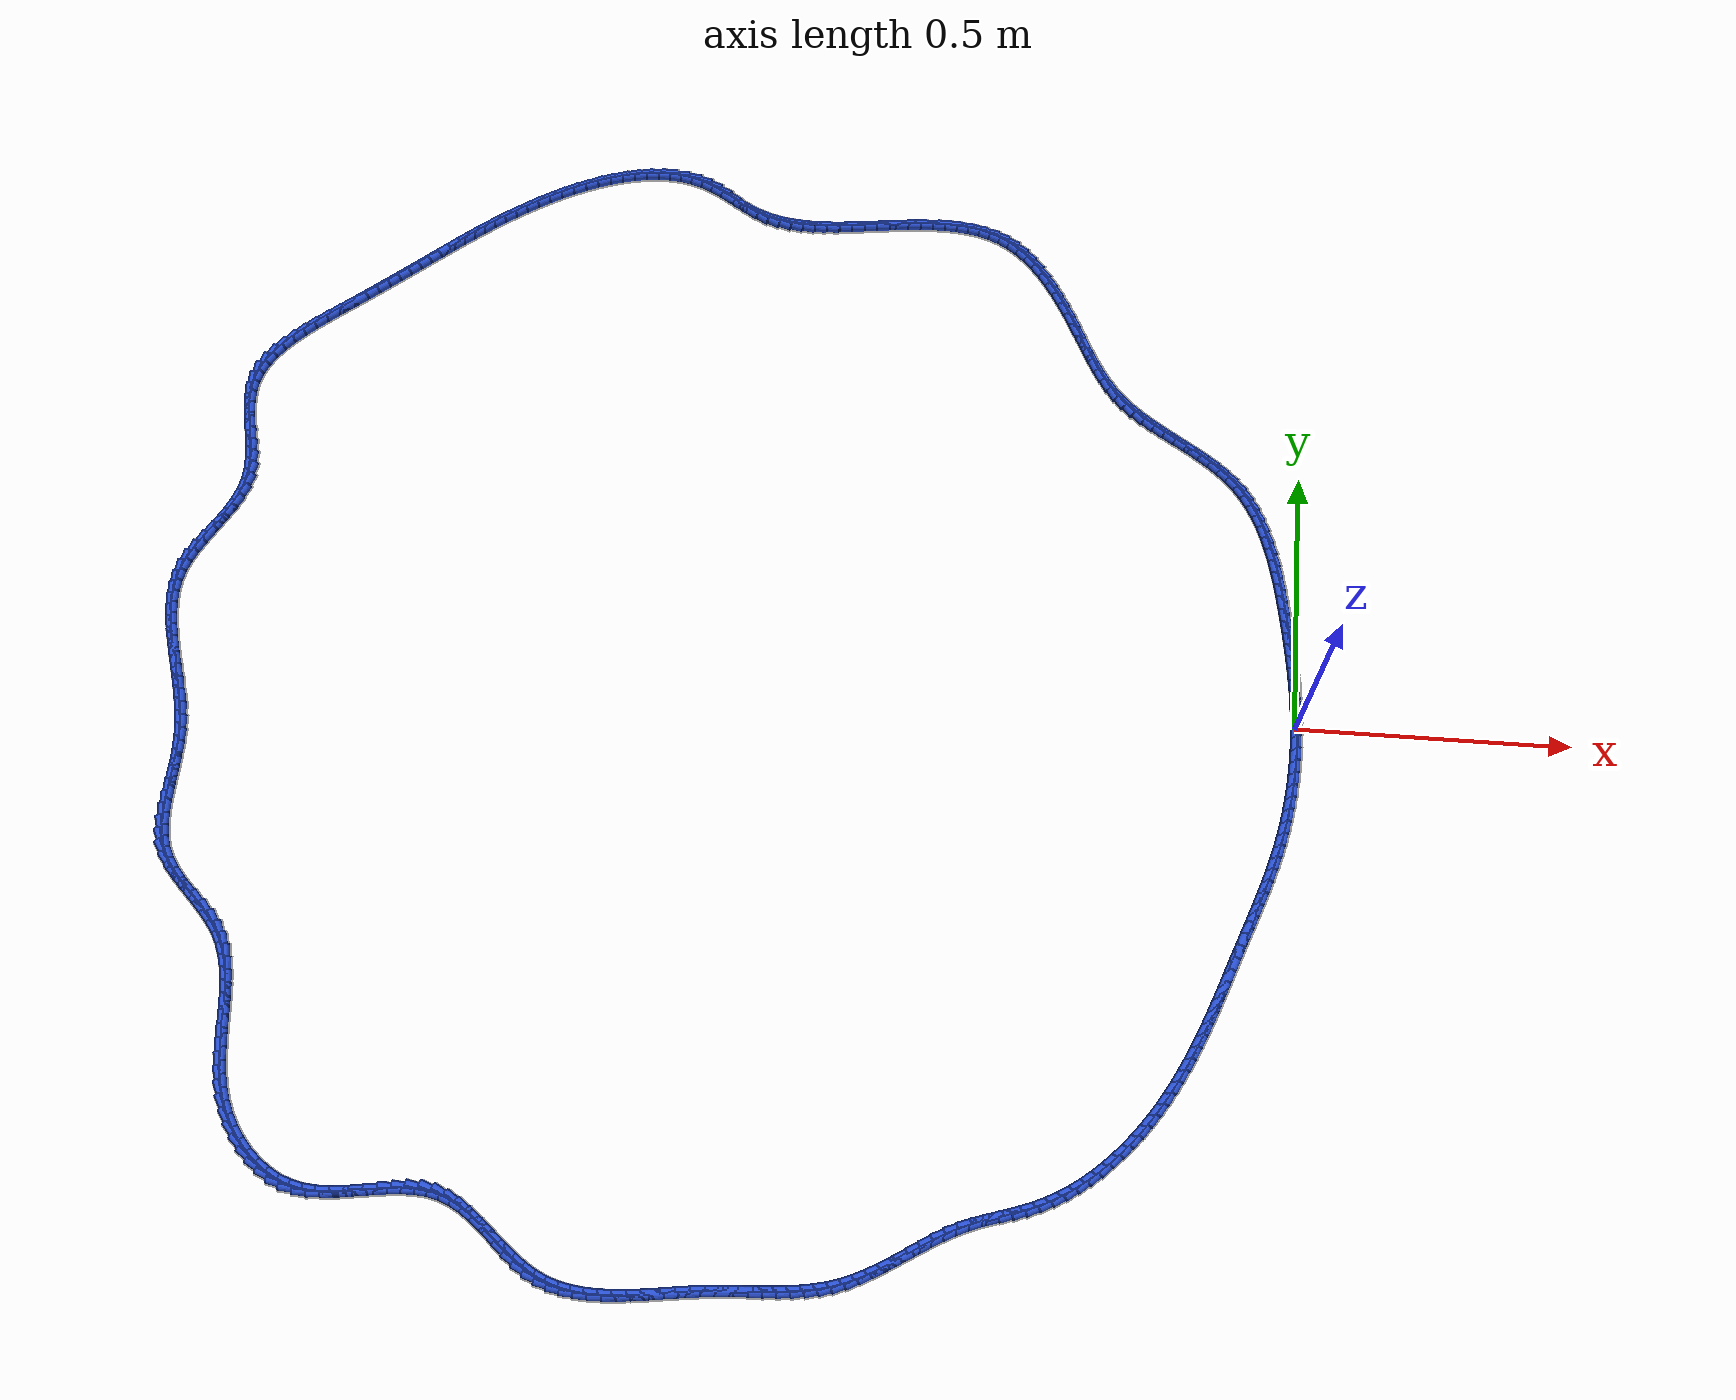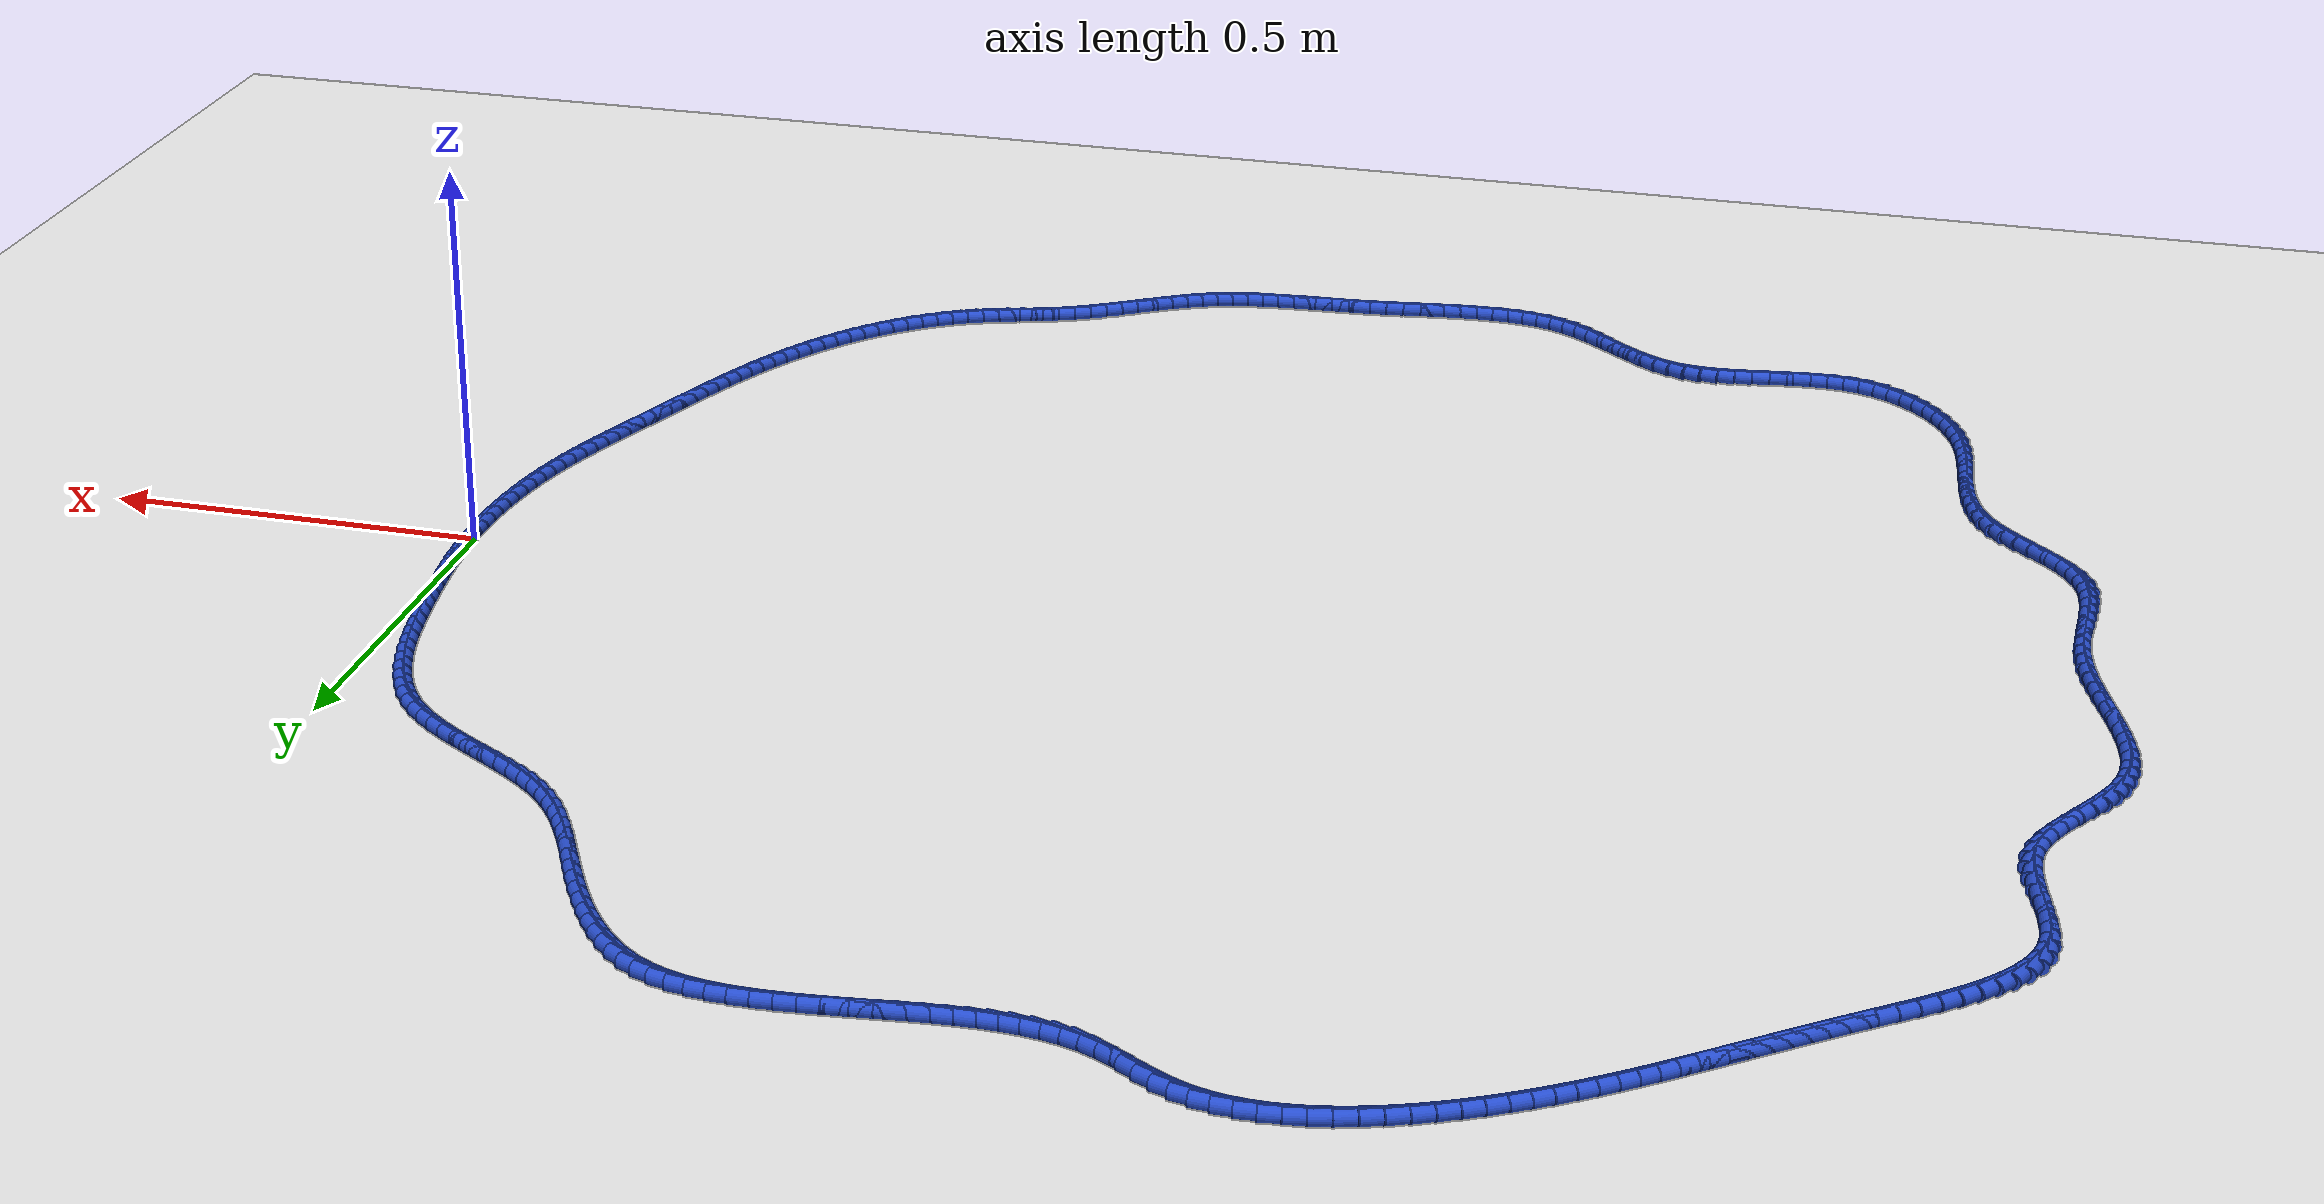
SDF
<sdf version="1.6">
 <world name="default">
  <light name="sun" type="directional">
   <pose>0 0 10 0 -0 0</pose>
   <diffuse>0.8 0.8 0.8 1</diffuse>
   <specular>0.2 0.2 0.2 1</specular>
   <attenuation>
    <range>1000</range>
    <constant>0.9</constant>
    <linear>0.01</linear>
    <quadratic>0.001</quadratic>
   </attenuation>
   <direction>-0.5 0.1 -0.9</direction>
  </light>
  <model name="ground_plane">
   <static>1</static>
   <link name="link">
    <collision name="collision">
     <geometry><plane><normal>0 0 1</normal><size>100 100</size></plane></geometry>
     <surface><friction><ode><mu>100</mu><mu2>50</mu2></ode></friction></surface>
    </collision>
    <visual name="visual">
     <cast_shadows>0</cast_shadows>
     <geometry><plane><normal>0 0 1</normal><size>100 100</size></plane></geometry>
     <material>
      <script><uri>file://media/materials/scripts/gazebo.material</uri><name>Gazebo/WhiteGlow</name></script>
     </material>
    </visual>
   </link>
  </model>
  <gravity>0 0 -9.8</gravity>
  <magnetic_field>6e-06 2.3e-05 -4.2e-05</magnetic_field>
  <atmosphere type="adiabatic"/>
  <physics name="default_physics" default="0" type="ode">
   <max_step_size>0.001</max_step_size>
   <real_time_factor>1</real_time_factor>
   <real_time_update_rate>1000</real_time_update_rate>
  </physics>
  <scene><ambient>0.4 0.4 0.4 1</ambient><background>0.7 0.7 0.7 1</background><shadows>1</shadows></scene>
  <spherical_coordinates>
   <surface_model>EARTH_WGS84</surface_model>
   <latitude_deg>0</latitude_deg>
   <longitude_deg>0</longitude_deg>
   <elevation>0</elevation>
   <heading_deg>0</heading_deg>
  </spherical_coordinates>
  <model name="line">
   <link name="link_0">
    <pose>-9.974659986866641e-18 0.0 0.01 0 1.57 -1.5426376400969413</pose>
    <collision name="collision">
     <geometry><cylinder><radius>0.01</radius><length>0.08</length></cylinder></geometry>
    </collision>
    <visual name="visual">
     <material>
      <script><name>Gazebo/Blue</name><uri>file://media/materials/scripts/gazebo.material</uri></script>
     </material>
     <geometry><cylinder><radius>0.01</radius><length>0.08</length></cylinder></geometry>
    </visual>
   </link>
   <link name="link_1">
    <pose>-0.0006535011654072775 0.02320166563133421 0.01 0 1.57 -1.5184669543189968</pose>
    <collision name="collision">
     <geometry><cylinder><radius>0.01</radius><length>0.08</length></cylinder></geometry>
    </collision>
    <visual name="visual">
     <material>
      <script><name>Gazebo/Blue</name><uri>file://media/materials/scripts/gazebo.material</uri></script>
     </material>
     <geometry><cylinder><radius>0.01</radius><length>0.08</length></cylinder></geometry>
    </visual>
   </link>
   <link name="link_2">
    <pose>-0.0018649368852563999 0.046330735921835814 0.01 0 1.57 -1.4961589771857828</pose>
    <collision name="collision">
     <geometry><cylinder><radius>0.01</radius><length>0.08</length></cylinder></geometry>
    </collision>
    <visual name="visual">
     <material>
      <script><name>Gazebo/Blue</name><uri>file://media/materials/scripts/gazebo.material</uri></script>
     </material>
     <geometry><cylinder><radius>0.01</radius><length>0.08</length></cylinder></geometry>
    </visual>
   </link>
   <link name="link_3">
    <pose>-0.0035916415821143303 0.06942235395193948 0.01 0 1.57 -1.4758306153682874</pose>
    <collision name="collision">
     <geometry><cylinder><radius>0.01</radius><length>0.08</length></cylinder></geometry>
    </collision>
    <visual name="visual">
     <material>
      <script><name>Gazebo/Blue</name><uri>file://media/materials/scripts/gazebo.material</uri></script>
     </material>
     <geometry><cylinder><radius>0.01</radius><length>0.08</length></cylinder></geometry>
    </visual>
   </link>
   <link name="link_4">
    <pose>-0.005790949678548022 0.09251166280207991 0.01 0 1.57 -1.4575714925606467</pose>
    <collision name="collision">
     <geometry><cylinder><radius>0.01</radius><length>0.08</length></cylinder></geometry>
    </collision>
    <visual name="visual">
     <material>
      <script><name>Gazebo/Blue</name><uri>file://media/materials/scripts/gazebo.material</uri></script>
     </material>
     <geometry><cylinder><radius>0.01</radius><length>0.08</length></cylinder></geometry>
    </visual>
   </link>
   <link name="link_5">
    <pose>-0.008420195597124423 0.11563380555269182 0.01 0 1.57 -1.4414448840320986</pose>
    <collision name="collision">
     <geometry><cylinder><radius>0.01</radius><length>0.08</length></cylinder></geometry>
    </collision>
    <visual name="visual">
     <material>
      <script><name>Gazebo/Blue</name><uri>file://media/materials/scripts/gazebo.material</uri></script>
     </material>
     <geometry><cylinder><radius>0.01</radius><length>0.08</length></cylinder></geometry>
    </visual>
   </link>
   <link name="link_6">
    <pose>-0.011436713760410486 0.13882392528420975 0.01 0 1.57 -1.427489329861225</pose>
    <collision name="collision">
     <geometry><cylinder><radius>0.01</radius><length>0.08</length></cylinder></geometry>
    </collision>
    <visual name="visual">
     <material>
      <script><name>Gazebo/Blue</name><uri>file://media/materials/scripts/gazebo.material</uri></script>
     </material>
     <geometry><cylinder><radius>0.01</radius><length>0.08</length></cylinder></geometry>
    </visual>
   </link>
   <link name="link_7">
    <pose>-0.01479783859097316 0.16211716507706855 0.01 0 1.57 -1.4157206980959294</pose>
    <collision name="collision">
     <geometry><cylinder><radius>0.01</radius><length>0.08</length></cylinder></geometry>
    </collision>
    <visual name="visual">
     <material>
      <script><name>Gazebo/Blue</name><uri>file://media/materials/scripts/gazebo.material</uri></script>
     </material>
     <geometry><cylinder><radius>0.01</radius><length>0.08</length></cylinder></geometry>
    </visual>
   </link>
   <link name="link_8">
    <pose>-0.018460904511379397 0.18554866801170278 0.01 0 1.57 -1.4061344901895956</pose>
    <collision name="collision">
     <geometry><cylinder><radius>0.01</radius><length>0.08</length></cylinder></geometry>
    </collision>
    <visual name="visual">
     <material>
      <script><name>Gazebo/Blue</name><uri>file://media/materials/scripts/gazebo.material</uri></script>
     </material>
     <geometry><cylinder><radius>0.01</radius><length>0.08</length></cylinder></geometry>
    </visual>
   </link>
   <link name="link_9">
    <pose>-0.02238324594419616 0.20915357716854716 0.01 0 1.57 -1.3981448148507345</pose>
    <collision name="collision">
     <geometry><cylinder><radius>0.01</radius><length>0.08</length></cylinder></geometry>
    </collision>
    <visual name="visual">
     <material>
      <script><name>Gazebo/Blue</name><uri>file://media/materials/scripts/gazebo.material</uri></script>
     </material>
     <geometry><cylinder><radius>0.01</radius><length>0.08</length></cylinder></geometry>
    </visual>
   </link>
   <link name="link_10">
    <pose>-0.026533933366463994 0.23295506724168624 0.01 0 1.57 -1.3869090481068425</pose>
    <collision name="collision">
     <geometry><cylinder><radius>0.01</radius><length>0.08</length></cylinder></geometry>
    </collision>
    <visual name="visual">
     <material>
      <script><name>Gazebo/Blue</name><uri>file://media/materials/scripts/gazebo.material</uri></script>
     </material>
     <geometry><cylinder><radius>0.01</radius><length>0.08</length></cylinder></geometry>
    </visual>
   </link>
   <link name="link_11">
    <pose>-0.030982543184908742 0.2568738173378114 0.01 0 1.57 -1.3699339599801506</pose>
    <collision name="collision">
     <geometry><cylinder><radius>0.01</radius><length>0.08</length></cylinder></geometry>
    </collision>
    <visual name="visual">
     <material>
      <script><name>Gazebo/Blue</name><uri>file://media/materials/scripts/gazebo.material</uri></script>
     </material>
     <geometry><cylinder><radius>0.01</radius><length>0.08</length></cylinder></geometry>
    </visual>
   </link>
   <link name="link_12">
    <pose>-0.03584971413699516 0.28077843338147307 0.01 0 1.57 -1.3470366569464325</pose>
    <collision name="collision">
     <geometry><cylinder><radius>0.01</radius><length>0.08</length></cylinder></geometry>
    </collision>
    <visual name="visual">
     <material>
      <script><name>Gazebo/Blue</name><uri>file://media/materials/scripts/gazebo.material</uri></script>
     </material>
     <geometry><cylinder><radius>0.01</radius><length>0.08</length></cylinder></geometry>
    </visual>
   </link>
   <link name="link_13">
    <pose>-0.04125648687033959 0.3045371114306874 0.01 0 1.57 -1.3179298845713576</pose>
    <collision name="collision">
     <geometry><cylinder><radius>0.01</radius><length>0.08</length></cylinder></geometry>
    </collision>
    <visual name="visual">
     <material>
      <script><name>Gazebo/Blue</name><uri>file://media/materials/scripts/gazebo.material</uri></script>
     </material>
     <geometry><cylinder><radius>0.01</radius><length>0.08</length></cylinder></geometry>
    </visual>
   </link>
   <link name="link_14">
    <pose>-0.04732390203255834 0.3280180475434704 0.01 0 1.57 -1.282217757556199</pose>
    <collision name="collision">
     <geometry><cylinder><radius>0.01</radius><length>0.08</length></cylinder></geometry>
    </collision>
    <visual name="visual">
     <material>
      <script><name>Gazebo/Blue</name><uri>file://media/materials/scripts/gazebo.material</uri></script>
     </material>
     <geometry><cylinder><radius>0.01</radius><length>0.08</length></cylinder></geometry>
    </visual>
   </link>
   <link name="link_15">
    <pose>-0.05417300027126774 0.35108943777783846 0.01 0 1.57 -1.239417628663699</pose>
    <collision name="collision">
     <geometry><cylinder><radius>0.01</radius><length>0.08</length></cylinder></geometry>
    </collision>
    <visual name="visual">
     <material>
      <script><name>Gazebo/Blue</name><uri>file://media/materials/scripts/gazebo.material</uri></script>
     </material>
     <geometry><cylinder><radius>0.01</radius><length>0.08</length></cylinder></geometry>
    </visual>
   </link>
   <link name="link_16">
    <pose>-0.061924822234084145 0.3736194781918077 0.01 0 1.57 -1.188995689473306</pose>
    <collision name="collision">
     <geometry><cylinder><radius>0.01</radius><length>0.08</length></cylinder></geometry>
    </collision>
    <visual name="visual">
     <material>
      <script><name>Gazebo/Blue</name><uri>file://media/materials/scripts/gazebo.material</uri></script>
     </material>
     <geometry><cylinder><radius>0.01</radius><length>0.08</length></cylinder></geometry>
    </visual>
   </link>
   <link name="link_17">
    <pose>-0.07070040856862389 0.3954763648433943 0.01 0 1.57 -1.1304249307770082</pose>
    <collision name="collision">
     <geometry><cylinder><radius>0.01</radius><length>0.08</length></cylinder></geometry>
    </collision>
    <visual name="visual">
     <material>
      <script><name>Gazebo/Blue</name><uri>file://media/materials/scripts/gazebo.material</uri></script>
     </material>
     <geometry><cylinder><radius>0.01</radius><length>0.08</length></cylinder></geometry>
    </visual>
   </link>
   <link name="link_18">
    <pose>-0.08062079992250326 0.4165282937906145 0.01 0 1.57 -1.0632745719719394</pose>
    <collision name="collision">
     <geometry><cylinder><radius>0.01</radius><length>0.08</length></cylinder></geometry>
    </collision>
    <visual name="visual">
     <material>
      <script><name>Gazebo/Blue</name><uri>file://media/materials/scripts/gazebo.material</uri></script>
     </material>
     <geometry><cylinder><radius>0.01</radius><length>0.08</length></cylinder></geometry>
    </visual>
   </link>
   <link name="link_19">
    <pose>-0.0918070369433386 0.43664346109148444 0.01 0 1.57 -0.9873367878217699</pose>
    <collision name="collision">
     <geometry><cylinder><radius>0.01</radius><length>0.08</length></cylinder></geometry>
    </collision>
    <visual name="visual">
     <material>
      <script><name>Gazebo/Blue</name><uri>file://media/materials/scripts/gazebo.material</uri></script>
     </material>
     <geometry><cylinder><radius>0.01</radius><length>0.08</length></cylinder></geometry>
    </visual>
   </link>
   <link name="link_20">
    <pose>-0.1043801602787463 0.4556900628040203 0.01 0 1.57 -0.9027858988831038</pose>
    <collision name="collision">
     <geometry><cylinder><radius>0.01</radius><length>0.08</length></cylinder></geometry>
    </collision>
    <visual name="visual">
     <material>
      <script><name>Gazebo/Blue</name><uri>file://media/materials/scripts/gazebo.material</uri></script>
     </material>
     <geometry><cylinder><radius>0.01</radius><length>0.08</length></cylinder></geometry>
    </visual>
   </link>
   <link name="link_21">
    <pose>-0.11846121057634267 0.4735362949862384 0.01 0 1.57 -0.8119439673539637</pose>
    <collision name="collision">
     <geometry><cylinder><radius>0.01</radius><length>0.08</length></cylinder></geometry>
    </collision>
    <visual name="visual">
     <material>
      <script><name>Gazebo/Blue</name><uri>file://media/materials/scripts/gazebo.material</uri></script>
     </material>
     <geometry><cylinder><radius>0.01</radius><length>0.08</length></cylinder></geometry>
    </visual>
   </link>
   <link name="link_22">
    <pose>-0.13414415011568492 0.49007477909193486 0.01 0 1.57 -0.7300866755986011</pose>
    <collision name="collision">
     <geometry><cylinder><radius>0.01</radius><length>0.08</length></cylinder></geometry>
    </collision>
    <visual name="visual">
     <material>
      <script><name>Gazebo/Blue</name><uri>file://media/materials/scripts/gazebo.material</uri></script>
     </material>
     <geometry><cylinder><radius>0.01</radius><length>0.08</length></cylinder></geometry>
    </visual>
   </link>
   <link name="link_23">
    <pose>-0.15128258714375062 0.5054149421948155 0.01 0 1.57 -0.6649232722668154</pose>
    <collision name="collision">
     <geometry><cylinder><radius>0.01</radius><length>0.08</length></cylinder></geometry>
    </collision>
    <visual name="visual">
     <material>
      <script><name>Gazebo/Blue</name><uri>file://media/materials/scripts/gazebo.material</uri></script>
     </material>
     <geometry><cylinder><radius>0.01</radius><length>0.08</length></cylinder></geometry>
    </visual>
   </link>
   <link name="link_24">
    <pose>-0.16960436447008062 0.5197796550804886 0.01 0 1.57 -0.6159699788188291</pose>
    <collision name="collision">
     <geometry><cylinder><radius>0.01</radius><length>0.08</length></cylinder></geometry>
    </collision>
    <visual name="visual">
     <material>
      <script><name>Gazebo/Blue</name><uri>file://media/materials/scripts/gazebo.material</uri></script>
     </material>
     <geometry><cylinder><radius>0.01</radius><length>0.08</length></cylinder></geometry>
    </visual>
   </link>
   <link name="link_25">
    <pose>-0.18883622405849584 0.5333927815261756 0.01 0 1.57 -0.5823932674288169</pose>
    <collision name="collision">
     <geometry><cylinder><radius>0.01</radius><length>0.08</length></cylinder></geometry>
    </collision>
    <visual name="visual">
     <material>
      <script><name>Gazebo/Blue</name><uri>file://media/materials/scripts/gazebo.material</uri></script>
     </material>
     <geometry><cylinder><radius>0.01</radius><length>0.08</length></cylinder></geometry>
    </visual>
   </link>
   <link name="link_26">
    <pose>-0.20870490787281715 0.5464781853090988 0.01 0 1.57 -0.5634322042427602</pose>
    <collision name="collision">
     <geometry><cylinder><radius>0.01</radius><length>0.08</length></cylinder></geometry>
    </collision>
    <visual name="visual">
     <material>
      <script><name>Gazebo/Blue</name><uri>file://media/materials/scripts/gazebo.material</uri></script>
     </material>
     <geometry><cylinder><radius>0.01</radius><length>0.08</length></cylinder></geometry>
    </visual>
   </link>
   <link name="link_27">
    <pose>-0.22893715787686544 0.5592597302064798 0.01 0 1.57 -0.5585975794039176</pose>
    <collision name="collision">
     <geometry><cylinder><radius>0.01</radius><length>0.08</length></cylinder></geometry>
    </collision>
    <visual name="visual">
     <material>
      <script><name>Gazebo/Blue</name><uri>file://media/materials/scripts/gazebo.material</uri></script>
     </material>
     <geometry><cylinder><radius>0.01</radius><length>0.08</length></cylinder></geometry>
    </visual>
   </link>
   <link name="link_28">
    <pose>-0.24925971603446193 0.5719612799955408 0.01 0 1.57 -0.5677641870239503</pose>
    <collision name="collision">
     <geometry><cylinder><radius>0.01</radius><length>0.08</length></cylinder></geometry>
    </collision>
    <visual name="visual">
     <material>
      <script><name>Gazebo/Blue</name><uri>file://media/materials/scripts/gazebo.material</uri></script>
     </material>
     <geometry><cylinder><radius>0.01</radius><length>0.08</length></cylinder></geometry>
    </visual>
   </link>
   <link name="link_29">
    <pose>-0.2693993243094273 0.5848066984535039 0.01 0 1.57 -0.5911923816275992</pose>
    <collision name="collision">
     <geometry><cylinder><radius>0.01</radius><length>0.08</length></cylinder></geometry>
    </collision>
    <visual name="visual">
     <material>
      <script><name>Gazebo/Blue</name><uri>file://media/materials/scripts/gazebo.material</uri></script>
     </material>
     <geometry><cylinder><radius>0.01</radius><length>0.08</length></cylinder></geometry>
    </visual>
   </link>
   <link name="link_30">
    <pose>-0.28908272466558255 0.5980198493575908 0.01 0 1.57 -0.6294884203891968</pose>
    <collision name="collision">
     <geometry><cylinder><radius>0.01</radius><length>0.08</length></cylinder></geometry>
    </collision>
    <visual name="visual">
     <material>
      <script><name>Gazebo/Blue</name><uri>file://media/materials/scripts/gazebo.material</uri></script>
     </material>
     <geometry><cylinder><radius>0.01</radius><length>0.08</length></cylinder></geometry>
    </visual>
   </link>
   <link name="link_31">
    <pose>-0.30803665906674865 0.6118245964850233 0.01 0 1.57 -0.6834847916722526</pose>
    <collision name="collision">
     <geometry><cylinder><radius>0.01</radius><length>0.08</length></cylinder></geometry>
    </collision>
    <visual name="visual">
     <material>
      <script><name>Gazebo/Blue</name><uri>file://media/materials/scripts/gazebo.material</uri></script>
     </material>
     <geometry><cylinder><radius>0.01</radius><length>0.08</length></cylinder></geometry>
    </visual>
   </link>
   <link name="link_32">
    <pose>-0.32598786947674646 0.6264448036130235 0.01 0 1.57 -0.7539965500688934</pose>
    <collision name="collision">
     <geometry><cylinder><radius>0.01</radius><length>0.08</length></cylinder></geometry>
    </collision>
    <visual name="visual">
     <material>
      <script><name>Gazebo/Blue</name><uri>file://media/materials/scripts/gazebo.material</uri></script>
     </material>
     <geometry><cylinder><radius>0.01</radius><length>0.08</length></cylinder></geometry>
    </visual>
   </link>
   <link name="link_33">
    <pose>-0.34266309785939714 0.6421043345188135 0.01 0 1.57 -0.838173663380497</pose>
    <collision name="collision">
     <geometry><cylinder><radius>0.01</radius><length>0.08</length></cylinder></geometry>
    </collision>
    <visual name="visual">
     <material>
      <script><name>Gazebo/Blue</name><uri>file://media/materials/scripts/gazebo.material</uri></script>
     </material>
     <geometry><cylinder><radius>0.01</radius><length>0.08</length></cylinder></geometry>
    </visual>
   </link>
   <link name="link_34">
    <pose>-0.3578489342899978 0.6589840176669219 0.01 0 1.57 -0.916460572727679</pose>
    <collision name="collision">
     <geometry><cylinder><radius>0.01</radius><length>0.08</length></cylinder></geometry>
    </collision>
    <visual name="visual">
     <material>
      <script><name>Gazebo/Blue</name><uri>file://media/materials/scripts/gazebo.material</uri></script>
     </material>
     <geometry><cylinder><radius>0.01</radius><length>0.08</length></cylinder></geometry>
    </visual>
   </link>
   <link name="link_35">
    <pose>-0.3716796703949959 0.6770146578434606 0.01 0 1.57 -0.9808450246990053</pose>
    <collision name="collision">
     <geometry><cylinder><radius>0.01</radius><length>0.08</length></cylinder></geometry>
    </collision>
    <visual name="visual">
     <material>
      <script><name>Gazebo/Blue</name><uri>file://media/materials/scripts/gazebo.material</uri></script>
     </material>
     <geometry><cylinder><radius>0.01</radius><length>0.08</length></cylinder></geometry>
    </visual>
   </link>
   <link name="link_36">
    <pose>-0.38441484419521005 0.6960369982166814 0.01 0 1.57 -1.0308762732187808</pose>
    <collision name="collision">
     <geometry><cylinder><radius>0.01</radius><length>0.08</length></cylinder></geometry>
    </collision>
    <visual name="visual">
     <material>
      <script><name>Gazebo/Blue</name><uri>file://media/materials/scripts/gazebo.material</uri></script>
     </material>
     <geometry><cylinder><radius>0.01</radius><length>0.08</length></cylinder></geometry>
    </visual>
   </link>
   <link name="link_37">
    <pose>-0.3963141603505799 0.7158916621287209 0.01 0 1.57 -1.0667205692190862</pose>
    <collision name="collision">
     <geometry><cylinder><radius>0.01</radius><length>0.08</length></cylinder></geometry>
    </collision>
    <visual name="visual">
     <material>
      <script><name>Gazebo/Blue</name><uri>file://media/materials/scripts/gazebo.material</uri></script>
     </material>
     <geometry><cylinder><radius>0.01</radius><length>0.08</length></cylinder></geometry>
    </visual>
   </link>
   <link name="link_38">
    <pose>-0.4076373235210451 0.7364192729217155 0.01 0 1.57 -1.0888372296079933</pose>
    <collision name="collision">
     <geometry><cylinder><radius>0.01</radius><length>0.08</length></cylinder></geometry>
    </collision>
    <visual name="visual">
     <material>
      <script><name>Gazebo/Blue</name><uri>file://media/materials/scripts/gazebo.material</uri></script>
     </material>
     <geometry><cylinder><radius>0.01</radius><length>0.08</length></cylinder></geometry>
    </visual>
   </link>
   <link name="link_39">
    <pose>-0.4186440383665456 0.7574604539378023 0.01 0 1.57 -1.0977600651861315</pose>
    <collision name="collision">
     <geometry><cylinder><radius>0.01</radius><length>0.08</length></cylinder></geometry>
    </collision>
    <visual name="visual">
     <material>
      <script><name>Gazebo/Blue</name><uri>file://media/materials/scripts/gazebo.material</uri></script>
     </material>
     <geometry><cylinder><radius>0.01</radius><length>0.08</length></cylinder></geometry>
    </visual>
   </link>
   <link name="link_40">
    <pose>-0.42959400954702076 0.7788558285191178 0.01 0 1.57 -1.0939775819097157</pose>
    <collision name="collision">
     <geometry><cylinder><radius>0.01</radius><length>0.08</length></cylinder></geometry>
    </collision>
    <visual name="visual">
     <material>
      <script><name>Gazebo/Blue</name><uri>file://media/materials/scripts/gazebo.material</uri></script>
     </material>
     <geometry><cylinder><radius>0.01</radius><length>0.08</length></cylinder></geometry>
    </visual>
   </link>
   <link name="link_41">
    <pose>-0.4407469417224104 0.8004460200077984 0.01 0 1.57 -1.0779288026242957</pose>
    <collision name="collision">
     <geometry><cylinder><radius>0.01</radius><length>0.08</length></cylinder></geometry>
    </collision>
    <visual name="visual">
     <material>
      <script><name>Gazebo/Blue</name><uri>file://media/materials/scripts/gazebo.material</uri></script>
     </material>
     <geometry><cylinder><radius>0.01</radius><length>0.08</length></cylinder></geometry>
    </visual>
   </link>
   <link name="link_42">
    <pose>-0.4523612055154255 0.822070965252481 0.01 0 1.57 -1.051876951484381</pose>
    <collision name="collision">
     <geometry><cylinder><radius>0.01</radius><length>0.08</length></cylinder></geometry>
    </collision>
    <visual name="visual">
     <material>
      <script><name>Gazebo/Blue</name><uri>file://media/materials/scripts/gazebo.material</uri></script>
     </material>
     <geometry><cylinder><radius>0.01</radius><length>0.08</length></cylinder></geometry>
    </visual>
   </link>
   <link name="link_43">
    <pose>-0.46461738413838594 0.8435305718203864 0.01 0 1.57 -1.0185852577578811</pose>
    <collision name="collision">
     <geometry><cylinder><radius>0.01</radius><length>0.08</length></cylinder></geometry>
    </collision>
    <visual name="visual">
     <material>
      <script><name>Gazebo/Blue</name><uri>file://media/materials/scripts/gazebo.material</uri></script>
     </material>
     <geometry><cylinder><radius>0.01</radius><length>0.08</length></cylinder></geometry>
    </visual>
   </link>
   <link name="link_44">
    <pose>-0.4775767692727611 0.8645633600409448 0.01 0 1.57 -0.9775618687917156</pose>
    <collision name="collision">
     <geometry><cylinder><radius>0.01</radius><length>0.08</length></cylinder></geometry>
    </collision>
    <visual name="visual">
     <material>
      <script><name>Gazebo/Blue</name><uri>file://media/materials/scripts/gazebo.material</uri></script>
     </material>
     <geometry><cylinder><radius>0.01</radius><length>0.08</length></cylinder></geometry>
    </visual>
   </link>
   <link name="link_45">
    <pose>-0.49129053900137 0.8849026458013198 0.01 0 1.57 -0.9277905162438524</pose>
    <collision name="collision">
     <geometry><cylinder><radius>0.01</radius><length>0.08</length></cylinder></geometry>
    </collision>
    <visual name="visual">
     <material>
      <script><name>Gazebo/Blue</name><uri>file://media/materials/scripts/gazebo.material</uri></script>
     </material>
     <geometry><cylinder><radius>0.01</radius><length>0.08</length></cylinder></geometry>
    </visual>
   </link>
   <link name="link_46">
    <pose>-0.5058098714070313 0.9042817449886734 0.01 0 1.57 -0.8680100710075115</pose>
    <collision name="collision">
     <geometry><cylinder><radius>0.01</radius><length>0.08</length></cylinder></geometry>
    </collision>
    <visual name="visual">
     <material>
      <script><name>Gazebo/Blue</name><uri>file://media/materials/scripts/gazebo.material</uri></script>
     </material>
     <geometry><cylinder><radius>0.01</radius><length>0.08</length></cylinder></geometry>
    </visual>
   </link>
   <link name="link_47">
    <pose>-0.521185944572564 0.9224339734901694 0.01 0 1.57 -0.7967714245222793</pose>
    <collision name="collision">
     <geometry><cylinder><radius>0.01</radius><length>0.08</length></cylinder></geometry>
    </collision>
    <visual name="visual">
     <material>
      <script><name>Gazebo/Blue</name><uri>file://media/materials/scripts/gazebo.material</uri></script>
     </material>
     <geometry><cylinder><radius>0.01</radius><length>0.08</length></cylinder></geometry>
    </visual>
   </link>
   <link name="link_48">
    <pose>-0.5374699365807867 0.9390926471929701 0.01 0 1.57 -0.7125793245817673</pose>
    <collision name="collision">
     <geometry><cylinder><radius>0.01</radius><length>0.08</length></cylinder></geometry>
    </collision>
    <visual name="visual">
     <material>
      <script><name>Gazebo/Blue</name><uri>file://media/materials/scripts/gazebo.material</uri></script>
     </material>
     <geometry><cylinder><radius>0.01</radius><length>0.08</length></cylinder></geometry>
    </visual>
   </link>
   <link name="link_49">
    <pose>-0.5547130255145186 0.9539910819842389 0.01 0 1.57 -0.6141795525885984</pose>
    <collision name="collision">
     <geometry><cylinder><radius>0.01</radius><length>0.08</length></cylinder></geometry>
    </collision>
    <visual name="visual">
     <material>
      <script><name>Gazebo/Blue</name><uri>file://media/materials/scripts/gazebo.material</uri></script>
     </material>
     <geometry><cylinder><radius>0.01</radius><length>0.08</length></cylinder></geometry>
    </visual>
   </link>
   <link name="link_50">
    <pose>-0.5729663894565782 0.9668625937511383 0.01 0 1.57 -0.5012842505350611</pose>
    <collision name="collision">
     <geometry><cylinder><radius>0.01</radius><length>0.08</length></cylinder></geometry>
    </collision>
    <visual name="visual">
     <material>
      <script><name>Gazebo/Blue</name><uri>file://media/materials/scripts/gazebo.material</uri></script>
     </material>
     <geometry><cylinder><radius>0.01</radius><length>0.08</length></cylinder></geometry>
    </visual>
   </link>
   <link name="link_51">
    <pose>-0.592279555345757 0.9774456522847644 0.01 0 1.57 -0.3844899023576935</pose>
    <collision name="collision">
     <geometry><cylinder><radius>0.01</radius><length>0.08</length></cylinder></geometry>
    </collision>
    <visual name="visual">
     <material>
      <script><name>Gazebo/Blue</name><uri>file://media/materials/scripts/gazebo.material</uri></script>
     </material>
     <geometry><cylinder><radius>0.01</radius><length>0.08</length></cylinder></geometry>
    </visual>
   </link>
   <link name="link_52">
    <pose>-0.6126366952544277 0.9856827269653262 0.01 0 1.57 -0.27895316610653775</pose>
    <collision name="collision">
     <geometry><cylinder><radius>0.01</radius><length>0.08</length></cylinder></geometry>
    </collision>
    <visual name="visual">
     <material>
      <script><name>Gazebo/Blue</name><uri>file://media/materials/scripts/gazebo.material</uri></script>
     </material>
     <geometry><cylinder><radius>0.01</radius><length>0.08</length></cylinder></geometry>
    </visual>
   </link>
   <link name="link_53">
    <pose>-0.6339364018168482 0.9917834160215503 0.01 0 1.57 -0.18716473958073807</pose>
    <collision name="collision">
     <geometry><cylinder><radius>0.01</radius><length>0.08</length></cylinder></geometry>
    </collision>
    <visual name="visual">
     <material>
      <script><name>Gazebo/Blue</name><uri>file://media/materials/scripts/gazebo.material</uri></script>
     </material>
     <geometry><cylinder><radius>0.01</radius><length>0.08</length></cylinder></geometry>
    </visual>
   </link>
   <link name="link_54">
    <pose>-0.6560714792130904 0.9959753858435743 0.01 0 1.57 -0.10938489917740066</pose>
    <collision name="collision">
     <geometry><cylinder><radius>0.01</radius><length>0.08</length></cylinder></geometry>
    </collision>
    <visual name="visual">
     <material>
      <script><name>Gazebo/Blue</name><uri>file://media/materials/scripts/gazebo.material</uri></script>
     </material>
     <geometry><cylinder><radius>0.01</radius><length>0.08</length></cylinder></geometry>
    </visual>
   </link>
   <link name="link_55">
    <pose>-0.6789347316232276 0.998486302821537 0.01 0 1.57 -0.04500111296149951</pose>
    <collision name="collision">
     <geometry><cylinder><radius>0.01</radius><length>0.08</length></cylinder></geometry>
    </collision>
    <visual name="visual">
     <material>
      <script><name>Gazebo/Blue</name><uri>file://media/materials/scripts/gazebo.material</uri></script>
     </material>
     <geometry><cylinder><radius>0.01</radius><length>0.08</length></cylinder></geometry>
    </visual>
   </link>
   <link name="link_56">
    <pose>-0.7024189632273317 0.9995438333455768 0.01 0 1.57 0.007008362409394319</pose>
    <collision name="collision">
     <geometry><cylinder><radius>0.01</radius><length>0.08</length></cylinder></geometry>
    </collision>
    <visual name="visual">
     <material>
      <script><name>Gazebo/Blue</name><uri>file://media/materials/scripts/gazebo.material</uri></script>
     </material>
     <geometry><cylinder><radius>0.01</radius><length>0.08</length></cylinder></geometry>
    </visual>
   </link>
   <link name="link_57">
    <pose>-0.7264169782054747 0.9993756438058317 0.01 0 1.57 0.047751511290795634</pose>
    <collision name="collision">
     <geometry><cylinder><radius>0.01</radius><length>0.08</length></cylinder></geometry>
    </collision>
    <visual name="visual">
     <material>
      <script><name>Gazebo/Blue</name><uri>file://media/materials/scripts/gazebo.material</uri></script>
     </material>
     <geometry><cylinder><radius>0.01</radius><length>0.08</length></cylinder></geometry>
    </visual>
   </link>
   <link name="link_58">
    <pose>-0.750821580737729 0.9982094005924401 0.01 0 1.57 0.07823341582187818</pose>
    <collision name="collision">
     <geometry><cylinder><radius>0.01</radius><length>0.08</length></cylinder></geometry>
    </collision>
    <visual name="visual">
     <material>
      <script><name>Gazebo/Blue</name><uri>file://media/materials/scripts/gazebo.material</uri></script>
     </material>
     <geometry><cylinder><radius>0.01</radius><length>0.08</length></cylinder></geometry>
    </visual>
   </link>
   <link name="link_59">
    <pose>-0.7755255750041672 0.9962727700955406 0.01 0 1.57 0.09926030155038158</pose>
    <collision name="collision">
     <geometry><cylinder><radius>0.01</radius><length>0.08</length></cylinder></geometry>
    </collision>
    <visual name="visual">
     <material>
      <script><name>Gazebo/Blue</name><uri>file://media/materials/scripts/gazebo.material</uri></script>
     </material>
     <geometry><cylinder><radius>0.01</radius><length>0.08</length></cylinder></geometry>
    </visual>
   </link>
   <link name="link_60">
    <pose>-0.8004217651848617 0.9937934187052713 0.01 0 1.57 0.111397309688451</pose>
    <collision name="collision">
     <geometry><cylinder><radius>0.01</radius><length>0.08</length></cylinder></geometry>
    </collision>
    <visual name="visual">
     <material>
      <script><name>Gazebo/Blue</name><uri>file://media/materials/scripts/gazebo.material</uri></script>
     </material>
     <geometry><cylinder><radius>0.01</radius><length>0.08</length></cylinder></geometry>
    </visual>
   </link>
   <link name="link_61">
    <pose>-0.8254029554598843 0.9909990128117703 0.01 0 1.57 0.11495212562805629</pose>
    <collision name="collision">
     <geometry><cylinder><radius>0.01</radius><length>0.08</length></cylinder></geometry>
    </collision>
    <visual name="visual">
     <material>
      <script><name>Gazebo/Blue</name><uri>file://media/materials/scripts/gazebo.material</uri></script>
     </material>
     <geometry><cylinder><radius>0.01</radius><length>0.08</length></cylinder></geometry>
    </visual>
   </link>
   <link name="link_62">
    <pose>-0.8503619500093078 0.9881172188051762 0.01 0 1.57 0.10990889441946415</pose>
    <collision name="collision">
     <geometry><cylinder><radius>0.01</radius><length>0.08</length></cylinder></geometry>
    </collision>
    <visual name="visual">
     <material>
      <script><name>Gazebo/Blue</name><uri>file://media/materials/scripts/gazebo.material</uri></script>
     </material>
     <geometry><cylinder><radius>0.01</radius><length>0.08</length></cylinder></geometry>
    </visual>
   </link>
   <link name="link_63">
    <pose>-0.8751955513953833 0.9853767412777447 0.01 0 1.57 0.09559367824908314</pose>
    <collision name="collision">
     <geometry><cylinder><radius>0.01</radius><length>0.08</length></cylinder></geometry>
    </collision>
    <visual name="visual">
     <material>
      <script><name>Gazebo/Blue</name><uri>file://media/materials/scripts/gazebo.material</uri></script>
     </material>
     <geometry><cylinder><radius>0.01</radius><length>0.08</length></cylinder></geometry>
    </visual>
   </link>
   <link name="link_64">
    <pose>-0.8998320131415078 0.9830144512382908 0.01 0 1.57 0.07137949419103348</pose>
    <collision name="collision">
     <geometry><cylinder><radius>0.01</radius><length>0.08</length></cylinder></geometry>
    </collision>
    <visual name="visual">
     <material>
      <script><name>Gazebo/Blue</name><uri>file://media/materials/scripts/gazebo.material</uri></script>
     </material>
     <geometry><cylinder><radius>0.01</radius><length>0.08</length></cylinder></geometry>
    </visual>
   </link>
   <link name="link_65">
    <pose>-0.9242144647584933 0.9812710823283006 0.01 0 1.57 0.036694373860054606</pose>
    <collision name="collision">
     <geometry><cylinder><radius>0.01</radius><length>0.08</length></cylinder></geometry>
    </collision>
    <visual name="visual">
     <material>
      <script><name>Gazebo/Blue</name><uri>file://media/materials/scripts/gazebo.material</uri></script>
     </material>
     <geometry><cylinder><radius>0.01</radius><length>0.08</length></cylinder></geometry>
    </visual>
   </link>
   <link name="link_66">
    <pose>-0.9482861243501449 0.9803873911929206 0.01 0 1.57 -0.00914345515145464</pose>
    <collision name="collision">
     <geometry><cylinder><radius>0.01</radius><length>0.08</length></cylinder></geometry>
    </collision>
    <visual name="visual">
     <material>
      <script><name>Gazebo/Blue</name><uri>file://media/materials/scripts/gazebo.material</uri></script>
     </material>
     <geometry><cylinder><radius>0.01</radius><length>0.08</length></cylinder></geometry>
    </visual>
   </link>
   <link name="link_67">
    <pose>-0.9719902100202689 0.9806041344772984 0.01 0 1.57 -0.06682271658181455</pose>
    <collision name="collision">
     <geometry><cylinder><radius>0.01</radius><length>0.08</length></cylinder></geometry>
    </collision>
    <visual name="visual">
     <material>
      <script><name>Gazebo/Blue</name><uri>file://media/materials/scripts/gazebo.material</uri></script>
     </material>
     <geometry><cylinder><radius>0.01</radius><length>0.08</length></cylinder></geometry>
    </visual>
   </link>
   <link name="link_68">
    <pose>-0.9952699398726703 0.9821620688265811 0.01 0 1.57 -0.1368616544842464</pose>
    <collision name="collision">
     <geometry><cylinder><radius>0.01</radius><length>0.08</length></cylinder></geometry>
    </collision>
    <visual name="visual">
     <material>
      <script><name>Gazebo/Blue</name><uri>file://media/materials/scripts/gazebo.material</uri></script>
     </material>
     <geometry><cylinder><radius>0.01</radius><length>0.08</length></cylinder></geometry>
    </visual>
   </link>
   <link name="link_69">
    <pose>-1.018068532011156 0.985301950885916 0.01 0 1.57 -0.2193439438538504</pose>
    <collision name="collision">
     <geometry><cylinder><radius>0.01</radius><length>0.08</length></cylinder></geometry>
    </collision>
    <visual name="visual">
     <material>
      <script><name>Gazebo/Blue</name><uri>file://media/materials/scripts/gazebo.material</uri></script>
     </material>
     <geometry><cylinder><radius>0.01</radius><length>0.08</length></cylinder></geometry>
    </visual>
   </link>
   <link name="link_70">
    <pose>-1.0403292045395311 0.9902645373004503 0.01 0 1.57 -0.3135891630760845</pose>
    <collision name="collision">
     <geometry><cylinder><radius>0.01</radius><length>0.08</length></cylinder></geometry>
    </collision>
    <visual name="visual">
     <material>
      <script><name>Gazebo/Blue</name><uri>file://media/materials/scripts/gazebo.material</uri></script>
     </material>
     <geometry><cylinder><radius>0.01</radius><length>0.08</length></cylinder></geometry>
    </visual>
   </link>
   <link name="link_71">
    <pose>-1.0619951755616022 0.9972905847153315 0.01 0 1.57 -0.41717820655222315</pose>
    <collision name="collision">
     <geometry><cylinder><radius>0.01</radius><length>0.08</length></cylinder></geometry>
    </collision>
    <visual name="visual">
     <material>
      <script><name>Gazebo/Blue</name><uri>file://media/materials/scripts/gazebo.material</uri></script>
     </material>
     <geometry><cylinder><radius>0.01</radius><length>0.08</length></cylinder></geometry>
    </visual>
   </link>
   <link name="link_72">
    <pose>-1.0830137298712708 1.0066058453347537 0.01 0 1.57 -0.5041663490242357</pose>
    <collision name="collision">
     <geometry><cylinder><radius>0.01</radius><length>0.08</length></cylinder></geometry>
    </collision>
    <visual name="visual">
     <material>
      <script><name>Gazebo/Blue</name><uri>file://media/materials/scripts/gazebo.material</uri></script>
     </material>
     <geometry><cylinder><radius>0.01</radius><length>0.08</length></cylinder></geometry>
    </visual>
   </link>
   <link name="link_73">
    <pose>-1.1034783453525545 1.0178966780143992 0.01 0 1.57 -0.5463712213394187</pose>
    <collision name="collision">
     <geometry><cylinder><radius>0.01</radius><length>0.08</length></cylinder></geometry>
    </collision>
    <visual name="visual">
     <material>
      <script><name>Gazebo/Blue</name><uri>file://media/materials/scripts/gazebo.material</uri></script>
     </material>
     <geometry><cylinder><radius>0.01</radius><length>0.08</length></cylinder></geometry>
    </visual>
   </link>
   <link name="link_74">
    <pose>-1.1236657990406393 1.0301731419103466 0.01 0 1.57 -0.5444186775033684</pose>
    <collision name="collision">
     <geometry><cylinder><radius>0.01</radius><length>0.08</length></cylinder></geometry>
    </collision>
    <visual name="visual">
     <material>
      <script><name>Gazebo/Blue</name><uri>file://media/materials/scripts/gazebo.material</uri></script>
     </material>
     <geometry><cylinder><radius>0.01</radius><length>0.08</length></cylinder></geometry>
    </visual>
   </link>
   <link name="link_75">
    <pose>-1.1438644750995501 1.0424024705698505 0.01 0 1.57 -0.49816332512608186</pose>
    <collision name="collision">
     <geometry><cylinder><radius>0.01</radius><length>0.08</length></cylinder></geometry>
    </collision>
    <visual name="visual">
     <material>
      <script><name>Gazebo/Blue</name><uri>file://media/materials/scripts/gazebo.material</uri></script>
     </material>
     <geometry><cylinder><radius>0.01</radius><length>0.08</length></cylinder></geometry>
    </visual>
   </link>
   <link name="link_76">
    <pose>-1.16436275769331 1.0535518975401656 0.01 0 1.57 -0.40585514558315117</pose>
    <collision name="collision">
     <geometry><cylinder><radius>0.01</radius><length>0.08</length></cylinder></geometry>
    </collision>
    <visual name="visual">
     <material>
      <script><name>Gazebo/Blue</name><uri>file://media/materials/scripts/gazebo.material</uri></script>
     </material>
     <geometry><cylinder><radius>0.01</radius><length>0.08</length></cylinder></geometry>
    </visual>
   </link>
   <link name="link_77">
    <pose>-1.1854420920754611 1.0626099447501587 0.01 0 1.57 -0.29059269104152613</pose>
    <collision name="collision">
     <geometry><cylinder><radius>0.01</radius><length>0.08</length></cylinder></geometry>
    </collision>
    <visual name="visual">
     <material>
      <script><name>Gazebo/Blue</name><uri>file://media/materials/scripts/gazebo.material</uri></script>
     </material>
     <geometry><cylinder><radius>0.01</radius><length>0.08</length></cylinder></geometry>
    </visual>
   </link>
   <link name="link_78">
    <pose>-1.2072037353344516 1.069117946336075 0.01 0 1.57 -0.18095843489095376</pose>
    <collision name="collision">
     <geometry><cylinder><radius>0.01</radius><length>0.08</length></cylinder></geometry>
    </collision>
    <visual name="visual">
     <material>
      <script><name>Gazebo/Blue</name><uri>file://media/materials/scripts/gazebo.material</uri></script>
     </material>
     <geometry><cylinder><radius>0.01</radius><length>0.08</length></cylinder></geometry>
    </visual>
   </link>
   <link name="link_79">
    <pose>-1.2295565140203688 1.073207607897364 0.01 0 1.57 -0.08002004956473212</pose>
    <collision name="collision">
     <geometry><cylinder><radius>0.01</radius><length>0.08</length></cylinder></geometry>
    </collision>
    <visual name="visual">
     <material>
      <script><name>Gazebo/Blue</name><uri>file://media/materials/scripts/gazebo.material</uri></script>
     </material>
     <geometry><cylinder><radius>0.01</radius><length>0.08</length></cylinder></geometry>
    </visual>
   </link>
   <link name="link_80">
    <pose>-1.25239986398118 1.075039445442667 0.01 0 1.57 0.011425766356564426</pose>
    <collision name="collision">
     <geometry><cylinder><radius>0.01</radius><length>0.08</length></cylinder></geometry>
    </collision>
    <visual name="visual">
     <material>
      <script><name>Gazebo/Blue</name><uri>file://media/materials/scripts/gazebo.material</uri></script>
     </material>
     <geometry><cylinder><radius>0.01</radius><length>0.08</length></cylinder></geometry>
    </visual>
   </link>
   <link name="link_81">
    <pose>-1.2756332210648524 1.074773974980625 0.01 0 1.57 0.09335035310838788</pose>
    <collision name="collision">
     <geometry><cylinder><radius>0.01</radius><length>0.08</length></cylinder></geometry>
    </collision>
    <visual name="visual">
     <material>
      <script><name>Gazebo/Blue</name><uri>file://media/materials/scripts/gazebo.material</uri></script>
     </material>
     <geometry><cylinder><radius>0.01</radius><length>0.08</length></cylinder></geometry>
    </visual>
   </link>
   <link name="link_82">
    <pose>-1.2991560211193534 1.0725717125198793 0.01 0 1.57 0.16623964003237704</pose>
    <collision name="collision">
     <geometry><cylinder><radius>0.01</radius><length>0.08</length></cylinder></geometry>
    </collision>
    <visual name="visual">
     <material>
      <script><name>Gazebo/Blue</name><uri>file://media/materials/scripts/gazebo.material</uri></script>
     </material>
     <geometry><cylinder><radius>0.01</radius><length>0.08</length></cylinder></geometry>
    </visual>
   </link>
   <link name="link_83">
    <pose>-1.3228676999926507 1.068593174069071 0.01 0 1.57 0.23086372103340913</pose>
    <collision name="collision">
     <geometry><cylinder><radius>0.01</radius><length>0.08</length></cylinder></geometry>
    </collision>
    <visual name="visual">
     <material>
      <script><name>Gazebo/Blue</name><uri>file://media/materials/scripts/gazebo.material</uri></script>
     </material>
     <geometry><cylinder><radius>0.01</radius><length>0.08</length></cylinder></geometry>
    </visual>
   </link>
   <link name="link_84">
    <pose>-1.3466676935327107 1.062998875636841 0.01 0 1.57 0.2881065337302563</pose>
    <collision name="collision">
     <geometry><cylinder><radius>0.01</radius><length>0.08</length></cylinder></geometry>
    </collision>
    <visual name="visual">
     <material>
      <script><name>Gazebo/Blue</name><uri>file://media/materials/scripts/gazebo.material</uri></script>
     </material>
     <geometry><cylinder><radius>0.01</radius><length>0.08</length></cylinder></geometry>
    </visual>
   </link>
   <link name="link_85">
    <pose>-1.3704554375875009 1.0559493332318306 0.01 0 1.57 0.33885732373718963</pose>
    <collision name="collision">
     <geometry><cylinder><radius>0.01</radius><length>0.08</length></cylinder></geometry>
    </collision>
    <visual name="visual">
     <material>
      <script><name>Gazebo/Blue</name><uri>file://media/materials/scripts/gazebo.material</uri></script>
     </material>
     <geometry><cylinder><radius>0.01</radius><length>0.08</length></cylinder></geometry>
    </visual>
   </link>
   <link name="link_86">
    <pose>-1.394130368004989 1.047605062862681 0.01 0 1.57 0.3839504416106811</pose>
    <collision name="collision">
     <geometry><cylinder><radius>0.01</radius><length>0.08</length></cylinder></geometry>
    </collision>
    <visual name="visual">
     <material>
      <script><name>Gazebo/Blue</name><uri>file://media/materials/scripts/gazebo.material</uri></script>
     </material>
     <geometry><cylinder><radius>0.01</radius><length>0.08</length></cylinder></geometry>
    </visual>
   </link>
   <link name="link_87">
    <pose>-1.4175919206331427 1.038126580538034 0.01 0 1.57 0.42413766194521507</pose>
    <collision name="collision">
     <geometry><cylinder><radius>0.01</radius><length>0.08</length></cylinder></geometry>
    </collision>
    <visual name="visual">
     <material>
      <script><name>Gazebo/Blue</name><uri>file://media/materials/scripts/gazebo.material</uri></script>
     </material>
     <geometry><cylinder><radius>0.01</radius><length>0.08</length></cylinder></geometry>
    </visual>
   </link>
   <link name="link_88">
    <pose>-1.4407395313199283 1.0276744022665294 0.01 0 1.57 0.4600801539726298</pose>
    <collision name="collision">
     <geometry><cylinder><radius>0.01</radius><length>0.08</length></cylinder></geometry>
    </collision>
    <visual name="visual">
     <material>
      <script><name>Gazebo/Blue</name><uri>file://media/materials/scripts/gazebo.material</uri></script>
     </material>
     <geometry><cylinder><radius>0.01</radius><length>0.08</length></cylinder></geometry>
    </visual>
   </link>
   <link name="link_89">
    <pose>-1.4634726359133141 1.0164090440568094 0.01 0 1.57 0.4923512137338881</pose>
    <collision name="collision">
     <geometry><cylinder><radius>0.01</radius><length>0.08</length></cylinder></geometry>
    </collision>
    <visual name="visual">
     <material>
      <script><name>Gazebo/Blue</name><uri>file://media/materials/scripts/gazebo.material</uri></script>
     </material>
     <geometry><cylinder><radius>0.01</radius><length>0.08</length></cylinder></geometry>
    </visual>
   </link>
   <link name="link_90">
    <pose>-1.4856906702612664 1.004491021917515 0.01 0 1.57 0.5214452828047791</pose>
    <collision name="collision">
     <geometry><cylinder><radius>0.01</radius><length>0.08</length></cylinder></geometry>
    </collision>
    <visual name="visual">
     <material>
      <script><name>Gazebo/Blue</name><uri>file://media/materials/scripts/gazebo.material</uri></script>
     </material>
     <geometry><cylinder><radius>0.01</radius><length>0.08</length></cylinder></geometry>
    </visual>
   </link>
   <link name="link_91">
    <pose>-1.5072932595968032 0.9920807122474734 0.01 0 1.57 0.5479879896261779</pose>
    <collision name="collision">
     <geometry><cylinder><radius>0.01</radius><length>0.08</length></cylinder></geometry>
    </collision>
    <visual name="visual">
     <material>
      <script><name>Gazebo/Blue</name><uri>file://media/materials/scripts/gazebo.material</uri></script>
     </material>
     <geometry><cylinder><radius>0.01</radius><length>0.08</length></cylinder></geometry>
    </visual>
   </link>
   <link name="link_92">
    <pose>-1.528225887309888 0.9793046859854214 0.01 0 1.57 0.5725260423239694</pose>
    <collision name="collision">
     <geometry><cylinder><radius>0.01</radius><length>0.08</length></cylinder></geometry>
    </collision>
    <visual name="visual">
     <material>
      <script><name>Gazebo/Blue</name><uri>file://media/materials/scripts/gazebo.material</uri></script>
     </material>
     <geometry><cylinder><radius>0.01</radius><length>0.08</length></cylinder></geometry>
    </visual>
   </link>
   <link name="link_93">
    <pose>-1.5485393089557906 0.9662119101230595 0.01 0 1.57 0.5949175428169848</pose>
    <collision name="collision">
     <geometry><cylinder><radius>0.01</radius><length>0.08</length></cylinder></geometry>
    </collision>
    <visual name="visual">
     <material>
      <script><name>Gazebo/Blue</name><uri>file://media/materials/scripts/gazebo.material</uri></script>
     </material>
     <geometry><cylinder><radius>0.01</radius><length>0.08</length></cylinder></geometry>
    </visual>
   </link>
   <link name="link_94">
    <pose>-1.5682989938779572 0.9528405050238737 0.01 0 1.57 0.614959366896582</pose>
    <collision name="collision">
     <geometry><cylinder><radius>0.01</radius><length>0.08</length></cylinder></geometry>
    </collision>
    <visual name="visual">
     <material>
      <script><name>Gazebo/Blue</name><uri>file://media/materials/scripts/gazebo.material</uri></script>
     </material>
     <geometry><cylinder><radius>0.01</radius><length>0.08</length></cylinder></geometry>
    </visual>
   </link>
   <link name="link_95">
    <pose>-1.5875704114198343 0.9392285910513496 0.01 0 1.57 0.6324721360858476</pose>
    <collision name="collision">
     <geometry><cylinder><radius>0.01</radius><length>0.08</length></cylinder></geometry>
    </collision>
    <visual name="visual">
     <material>
      <script><name>Gazebo/Blue</name><uri>file://media/materials/scripts/gazebo.material</uri></script>
     </material>
     <geometry><cylinder><radius>0.01</radius><length>0.08</length></cylinder></geometry>
    </visual>
   </link>
   <link name="link_96">
    <pose>-1.6064190309248698 0.9254142885689727 0.01 0 1.57 0.6473009762218896</pose>
    <collision name="collision">
     <geometry><cylinder><radius>0.01</radius><length>0.08</length></cylinder></geometry>
    </collision>
    <visual name="visual">
     <material>
      <script><name>Gazebo/Blue</name><uri>file://media/materials/scripts/gazebo.material</uri></script>
     </material>
     <geometry><cylinder><radius>0.01</radius><length>0.08</length></cylinder></geometry>
    </visual>
   </link>
   <link name="link_97">
    <pose>-1.624910321736509 0.9114357179402286 0.01 0 1.57 0.6593155275022328</pose>
    <collision name="collision">
     <geometry><cylinder><radius>0.01</radius><length>0.08</length></cylinder></geometry>
    </collision>
    <visual name="visual">
     <material>
      <script><name>Gazebo/Blue</name><uri>file://media/materials/scripts/gazebo.material</uri></script>
     </material>
     <geometry><cylinder><radius>0.01</radius><length>0.08</length></cylinder></geometry>
    </visual>
   </link>
   <link name="link_98">
    <pose>-1.6431097531981997 0.8973309995286032 0.01 0 1.57 0.6684094611919306</pose>
    <collision name="collision">
     <geometry><cylinder><radius>0.01</radius><length>0.08</length></cylinder></geometry>
    </collision>
    <visual name="visual">
     <material>
      <script><name>Gazebo/Blue</name><uri>file://media/materials/scripts/gazebo.material</uri></script>
     </material>
     <geometry><cylinder><radius>0.01</radius><length>0.08</length></cylinder></geometry>
    </visual>
   </link>
   <link name="link_99">
    <pose>-1.6610827946533886 0.8831382536975818 0.01 0 1.57 0.674499769587454</pose>
    <collision name="collision">
     <geometry><cylinder><radius>0.01</radius><length>0.08</length></cylinder></geometry>
    </collision>
    <visual name="visual">
     <material>
      <script><name>Gazebo/Blue</name><uri>file://media/materials/scripts/gazebo.material</uri></script>
     </material>
     <geometry><cylinder><radius>0.01</radius><length>0.08</length></cylinder></geometry>
    </visual>
   </link>
   <link name="link_100">
    <pose>-1.6788949154455226 0.8688956008106505 0.01 0 1.57 0.6775260787528726</pose>
    <collision name="collision">
     <geometry><cylinder><radius>0.01</radius><length>0.08</length></cylinder></geometry>
    </collision>
    <visual name="visual">
     <material>
      <script><name>Gazebo/Blue</name><uri>file://media/materials/scripts/gazebo.material</uri></script>
     </material>
     <geometry><cylinder><radius>0.01</radius><length>0.08</length></cylinder></geometry>
    </visual>
   </link>
   <link name="link_101">
    <pose>-1.696611584918048 0.8546411612312947 0.01 0 1.57 0.6775412201851119</pose>
    <collision name="collision">
     <geometry><cylinder><radius>0.01</radius><length>0.08</length></cylinder></geometry>
    </collision>
    <visual name="visual">
     <material>
      <script><name>Gazebo/Blue</name><uri>file://media/materials/scripts/gazebo.material</uri></script>
     </material>
     <geometry><cylinder><radius>0.01</radius><length>0.08</length></cylinder></geometry>
    </visual>
   </link>
   <link name="link_102">
    <pose>-1.7142984869347342 0.8404102307143501 0.01 0 1.57 0.6759508668978722</pose>
    <collision name="collision">
     <geometry><cylinder><radius>0.01</radius><length>0.08</length></cylinder></geometry>
    </collision>
    <visual name="visual">
     <material>
      <script><name>Gazebo/Blue</name><uri>file://media/materials/scripts/gazebo.material</uri></script>
     </material>
     <geometry><cylinder><radius>0.01</radius><length>0.08</length></cylinder></geometry>
    </visual>
   </link>
   <link name="link_103">
    <pose>-1.7320246478381358 0.8261940942916053 0.01 0 1.57 0.6738919612600929</pose>
    <collision name="collision">
     <geometry><cylinder><radius>0.01</radius><length>0.08</length></cylinder></geometry>
    </collision>
    <visual name="visual">
     <material>
      <script><name>Gazebo/Blue</name><uri>file://media/materials/scripts/gazebo.material</uri></script>
     </material>
     <geometry><cylinder><radius>0.01</radius><length>0.08</length></cylinder></geometry>
    </visual>
   </link>
   <link name="link_104">
    <pose>-1.7498617365782736 0.8119492415412916 0.01 0 1.57 0.6714235759140815</pose>
    <collision name="collision">
     <geometry><cylinder><radius>0.01</radius><length>0.08</length></cylinder></geometry>
    </collision>
    <visual name="visual">
     <material>
      <script><name>Gazebo/Blue</name><uri>file://media/materials/scripts/gazebo.material</uri></script>
     </material>
     <geometry><cylinder><radius>0.01</radius><length>0.08</length></cylinder></geometry>
    </visual>
   </link>
   <link name="link_105">
    <pose>-1.7678814942246637 0.7976312124376699 0.01 0 1.57 0.6685823350916043</pose>
    <collision name="collision">
     <geometry><cylinder><radius>0.01</radius><length>0.08</length></cylinder></geometry>
    </collision>
    <visual name="visual">
     <material>
      <script><name>Gazebo/Blue</name><uri>file://media/materials/scripts/gazebo.material</uri></script>
     </material>
     <geometry><cylinder><radius>0.01</radius><length>0.08</length></cylinder></geometry>
    </visual>
   </link>
   <link name="link_106">
    <pose>-1.7861556618468224 0.7831955469550019 0.01 0 1.57 0.6654113985714086</pose>
    <collision name="collision">
     <geometry><cylinder><radius>0.01</radius><length>0.08</length></cylinder></geometry>
    </collision>
    <visual name="visual">
     <material>
      <script><name>Gazebo/Blue</name><uri>file://media/materials/scripts/gazebo.material</uri></script>
     </material>
     <geometry><cylinder><radius>0.01</radius><length>0.08</length></cylinder></geometry>
    </visual>
   </link>
   <link name="link_107">
    <pose>-1.8047559805142663 0.7685977850675493 0.01 0 1.57 0.6619585963277157</pose>
    <collision name="collision">
     <geometry><cylinder><radius>0.01</radius><length>0.08</length></cylinder></geometry>
    </collision>
    <visual name="visual">
     <material>
      <script><name>Gazebo/Blue</name><uri>file://media/materials/scripts/gazebo.material</uri></script>
     </material>
     <geometry><cylinder><radius>0.01</radius><length>0.08</length></cylinder></geometry>
    </visual>
   </link>
   <link name="link_108">
    <pose>-1.823754191296511 0.7537934667495734 0.01 0 1.57 0.6582745740885197</pose>
    <collision name="collision">
     <geometry><cylinder><radius>0.01</radius><length>0.08</length></cylinder></geometry>
    </collision>
    <visual name="visual">
     <material>
      <script><name>Gazebo/Blue</name><uri>file://media/materials/scripts/gazebo.material</uri></script>
     </material>
     <geometry><cylinder><radius>0.01</radius><length>0.08</length></cylinder></geometry>
    </visual>
   </link>
   <link name="link_109">
    <pose>-1.8432220310571614 0.7387381318099389 0.01 0 1.57 0.6567263850847767</pose>
    <collision name="collision">
     <geometry><cylinder><radius>0.01</radius><length>0.08</length></cylinder></geometry>
    </collision>
    <visual name="visual">
     <material>
      <script><name>Gazebo/Blue</name><uri>file://media/materials/scripts/gazebo.material</uri></script>
     </material>
     <geometry><cylinder><radius>0.01</radius><length>0.08</length></cylinder></geometry>
    </visual>
   </link>
   <link name="link_110">
    <pose>-1.8631402223879252 0.7233837409427062 0.01 0 1.57 0.6653962548452813</pose>
    <collision name="collision">
     <geometry><cylinder><radius>0.01</radius><length>0.08</length></cylinder></geometry>
    </collision>
    <visual name="visual">
     <material>
      <script><name>Gazebo/Blue</name><uri>file://media/materials/scripts/gazebo.material</uri></script>
     </material>
     <geometry><cylinder><radius>0.01</radius><length>0.08</length></cylinder></geometry>
    </visual>
   </link>
   <link name="link_111">
    <pose>-1.883163836950601 0.7076694486958192 0.01 0 1.57 0.6860476418491631</pose>
    <collision name="collision">
     <geometry><cylinder><radius>0.01</radius><length>0.08</length></cylinder></geometry>
    </collision>
    <visual name="visual">
     <material>
      <script><name>Gazebo/Blue</name><uri>file://media/materials/scripts/gazebo.material</uri></script>
     </material>
     <geometry><cylinder><radius>0.01</radius><length>0.08</length></cylinder></geometry>
    </visual>
   </link>
   <link name="link_112">
    <pose>-1.9028751412966332 0.6915315465734059 0.01 0 1.57 0.719325622201434</pose>
    <collision name="collision">
     <geometry><cylinder><radius>0.01</radius><length>0.08</length></cylinder></geometry>
    </collision>
    <visual name="visual">
     <material>
      <script><name>Gazebo/Blue</name><uri>file://media/materials/scripts/gazebo.material</uri></script>
     </material>
     <geometry><cylinder><radius>0.01</radius><length>0.08</length></cylinder></geometry>
    </visual>
   </link>
   <link name="link_113">
    <pose>-1.9218564019774642 0.6749063260795942 0.01 0 1.57 0.7666274103440321</pose>
    <collision name="collision">
     <geometry><cylinder><radius>0.01</radius><length>0.08</length></cylinder></geometry>
    </collision>
    <visual name="visual">
     <material>
      <script><name>Gazebo/Blue</name><uri>file://media/materials/scripts/gazebo.material</uri></script>
     </material>
     <geometry><cylinder><radius>0.01</radius><length>0.08</length></cylinder></geometry>
    </visual>
   </link>
   <link name="link_114">
    <pose>-1.9396898855445364 0.6577300787185122 0.01 0 1.57 0.8300852586810039</pose>
    <collision name="collision">
     <geometry><cylinder><radius>0.01</radius><length>0.08</length></cylinder></geometry>
    </collision>
    <visual name="visual">
     <material>
      <script><name>Gazebo/Blue</name><uri>file://media/materials/scripts/gazebo.material</uri></script>
     </material>
     <geometry><cylinder><radius>0.01</radius><length>0.08</length></cylinder></geometry>
    </visual>
   </link>
   <link name="link_115">
    <pose>-1.9559578585492932 0.6399390959942876 0.01 0 1.57 0.9124705681648018</pose>
    <collision name="collision">
     <geometry><cylinder><radius>0.01</radius><length>0.08</length></cylinder></geometry>
    </collision>
    <visual name="visual">
     <material>
      <script><name>Gazebo/Blue</name><uri>file://media/materials/scripts/gazebo.material</uri></script>
     </material>
     <geometry><cylinder><radius>0.01</radius><length>0.08</length></cylinder></geometry>
    </visual>
   </link>
   <link name="link_116">
    <pose>-1.9702425875431766 0.6214696694110482 0.01 0 1.57 1.0168324996953533</pose>
    <collision name="collision">
     <geometry><cylinder><radius>0.01</radius><length>0.08</length></cylinder></geometry>
    </collision>
    <visual name="visual">
     <material>
      <script><name>Gazebo/Blue</name><uri>file://media/materials/scripts/gazebo.material</uri></script>
     </material>
     <geometry><cylinder><radius>0.01</radius><length>0.08</length></cylinder></geometry>
    </visual>
   </link>
   <link name="link_117">
    <pose>-1.9821263390776303 0.6022580904729227 0.01 0 1.57 1.1455689389465915</pose>
    <collision name="collision">
     <geometry><cylinder><radius>0.01</radius><length>0.08</length></cylinder></geometry>
    </collision>
    <visual name="visual">
     <material>
      <script><name>Gazebo/Blue</name><uri>file://media/materials/scripts/gazebo.material</uri></script>
     </material>
     <geometry><cylinder><radius>0.01</radius><length>0.08</length></cylinder></geometry>
    </visual>
   </link>
   <link name="link_118">
    <pose>-1.9911913797040959 0.5822406506840376 0.01 0 1.57 1.298665383325481</pose>
    <collision name="collision">
     <geometry><cylinder><radius>0.01</radius><length>0.08</length></cylinder></geometry>
    </collision>
    <visual name="visual">
     <material>
      <script><name>Gazebo/Blue</name><uri>file://media/materials/scripts/gazebo.material</uri></script>
     </material>
     <geometry><cylinder><radius>0.01</radius><length>0.08</length></cylinder></geometry>
    </visual>
   </link>
   <link name="link_119">
    <pose>-1.997019975974018 0.5613536415485219 0.01 0 1.57 1.4663684896630989</pose>
    <collision name="collision">
     <geometry><cylinder><radius>0.01</radius><length>0.08</length></cylinder></geometry>
    </collision>
    <visual name="visual">
     <material>
      <script><name>Gazebo/Blue</name><uri>file://media/materials/scripts/gazebo.material</uri></script>
     </material>
     <geometry><cylinder><radius>0.01</radius><length>0.08</length></cylinder></geometry>
    </visual>
   </link>
   <link name="link_120">
    <pose>-1.9993046706888136 0.539555012600101 0.01 0 1.57 -1.5369145867809686</pose>
    <collision name="collision">
     <geometry><cylinder><radius>0.01</radius><length>0.08</length></cylinder></geometry>
    </collision>
    <visual name="visual">
     <material>
      <script><name>Gazebo/Blue</name><uri>file://media/materials/scripts/gazebo.material</uri></script>
     </material>
     <geometry><cylinder><radius>0.01</radius><length>0.08</length></cylinder></geometry>
    </visual>
   </link>
   <link name="link_121">
    <pose>-1.998538818969266 0.516959991271588 0.01 0 1.57 -1.4435254099046584</pose>
    <collision name="collision">
     <geometry><cylinder><radius>0.01</radius><length>0.08</length></cylinder></geometry>
    </collision>
    <visual name="visual">
     <material>
      <script><name>Gazebo/Blue</name><uri>file://media/materials/scripts/gazebo.material</uri></script>
     </material>
     <geometry><cylinder><radius>0.01</radius><length>0.08</length></cylinder></geometry>
    </visual>
   </link>
   <link name="link_122">
    <pose>-1.9955692209444018 0.4937532208713949 0.01 0 1.57 -1.3897971148266666</pose>
    <collision name="collision">
     <geometry><cylinder><radius>0.01</radius><length>0.08</length></cylinder></geometry>
    </collision>
    <visual name="visual">
     <material>
      <script><name>Gazebo/Blue</name><uri>file://media/materials/scripts/gazebo.material</uri></script>
     </material>
     <geometry><cylinder><radius>0.01</radius><length>0.08</length></cylinder></geometry>
    </visual>
   </link>
   <link name="link_123">
    <pose>-1.9912442297810167 0.4701196497213701 0.01 0 1.57 -1.3711084108584073</pose>
    <collision name="collision">
     <geometry><cylinder><radius>0.01</radius><length>0.08</length></cylinder></geometry>
    </collision>
    <visual name="visual">
     <material>
      <script><name>Gazebo/Blue</name><uri>file://media/materials/scripts/gazebo.material</uri></script>
     </material>
     <geometry><cylinder><radius>0.01</radius><length>0.08</length></cylinder></geometry>
    </visual>
   </link>
   <link name="link_124">
    <pose>-1.98641219864591 0.4462442261433631 0.01 0 1.57 -1.3853108756747943</pose>
    <collision name="collision">
     <geometry><cylinder><radius>0.01</radius><length>0.08</length></cylinder></geometry>
    </collision>
    <visual name="visual">
     <material>
      <script><name>Gazebo/Blue</name><uri>file://media/materials/scripts/gazebo.material</uri></script>
     </material>
     <geometry><cylinder><radius>0.01</radius><length>0.08</length></cylinder></geometry>
    </visual>
   </link>
   <link name="link_125">
    <pose>-1.9819214807058771 0.4223118984592219 0.01 0 1.57 -1.4330004565943313</pose>
    <collision name="collision">
     <geometry><cylinder><radius>0.01</radius><length>0.08</length></cylinder></geometry>
    </collision>
    <visual name="visual">
     <material>
      <script><name>Gazebo/Blue</name><uri>file://media/materials/scripts/gazebo.material</uri></script>
     </material>
     <geometry><cylinder><radius>0.01</radius><length>0.08</length></cylinder></geometry>
    </visual>
   </link>
   <link name="link_126">
    <pose>-1.9786204291277154 0.3985076149907955 0.01 0 1.57 -1.5170820753851815</pose>
    <collision name="collision">
     <geometry><cylinder><radius>0.01</radius><length>0.08</length></cylinder></geometry>
    </collision>
    <visual name="visual">
     <material>
      <script><name>Gazebo/Blue</name><uri>file://media/materials/scripts/gazebo.material</uri></script>
     </material>
     <geometry><cylinder><radius>0.01</radius><length>0.08</length></cylinder></geometry>
    </visual>
   </link>
   <link name="link_127">
    <pose>-1.9773573970782232 0.37501632405993296 0.01 0 1.57 1.5003128374319135</pose>
    <collision name="collision">
     <geometry><cylinder><radius>0.01</radius><length>0.08</length></cylinder></geometry>
    </collision>
    <visual name="visual">
     <material>
      <script><name>Gazebo/Blue</name><uri>file://media/materials/scripts/gazebo.material</uri></script>
     </material>
     <geometry><cylinder><radius>0.01</radius><length>0.08</length></cylinder></geometry>
    </visual>
   </link>
   <link name="link_128">
    <pose>-1.9789807377241968 0.35202297398848276 0.01 0 1.57 1.3452930806433667</pose>
    <collision name="collision">
     <geometry><cylinder><radius>0.01</radius><length>0.08</length></cylinder></geometry>
    </collision>
    <visual name="visual">
     <material>
      <script><name>Gazebo/Blue</name><uri>file://media/materials/scripts/gazebo.material</uri></script>
     </material>
     <geometry><cylinder><radius>0.01</radius><length>0.08</length></cylinder></geometry>
    </visual>
   </link>
   <link name="link_129">
    <pose>-1.9841086442846025 0.3296699054889841 0.01 0 1.57 1.2120655142657806</pose>
    <collision name="collision">
     <geometry><cylinder><radius>0.01</radius><length>0.08</length></cylinder></geometry>
    </collision>
    <visual name="visual">
     <material>
      <script><name>Gazebo/Blue</name><uri>file://media/materials/scripts/gazebo.material</uri></script>
     </material>
     <geometry><cylinder><radius>0.01</radius><length>0.08</length></cylinder></geometry>
    </visual>
   </link>
   <link name="link_130">
    <pose>-1.9922720501158213 0.30789818383974016 0.01 0 1.57 1.1163984955807882</pose>
    <collision name="collision">
     <geometry><cylinder><radius>0.01</radius><length>0.08</length></cylinder></geometry>
    </collision>
    <visual name="visual">
     <material>
      <script><name>Gazebo/Blue</name><uri>file://media/materials/scripts/gazebo.material</uri></script>
     </material>
     <geometry><cylinder><radius>0.01</radius><length>0.08</length></cylinder></geometry>
    </visual>
   </link>
   <link name="link_131">
    <pose>-2.0026811446956736 0.28658949765515185 0.01 0 1.57 1.0557766887231061</pose>
    <collision name="collision">
     <geometry><cylinder><radius>0.01</radius><length>0.08</length></cylinder></geometry>
    </collision>
    <visual name="visual">
     <material>
      <script><name>Gazebo/Blue</name><uri>file://media/materials/scripts/gazebo.material</uri></script>
     </material>
     <geometry><cylinder><radius>0.01</radius><length>0.08</length></cylinder></geometry>
    </visual>
   </link>
   <link name="link_132">
    <pose>-2.0145460712005607 0.26562552697822034 0.01 0 1.57 1.0272498489067783</pose>
    <collision name="collision">
     <geometry><cylinder><radius>0.01</radius><length>0.08</length></cylinder></geometry>
    </collision>
    <visual name="visual">
     <material>
      <script><name>Gazebo/Blue</name><uri>file://media/materials/scripts/gazebo.material</uri></script>
     </material>
     <geometry><cylinder><radius>0.01</radius><length>0.08</length></cylinder></geometry>
    </visual>
   </link>
   <link name="link_133">
    <pose>-2.02707697280688 0.24488795185194703 0.01 0 1.57 1.029332427604703</pose>
    <collision name="collision">
     <geometry><cylinder><radius>0.01</radius><length>0.08</length></cylinder></geometry>
    </collision>
    <visual name="visual">
     <material>
      <script><name>Gazebo/Blue</name><uri>file://media/materials/scripts/gazebo.material</uri></script>
     </material>
     <geometry><cylinder><radius>0.01</radius><length>0.08</length></cylinder></geometry>
    </visual>
   </link>
   <link name="link_134">
    <pose>-2.039483992691031 0.22425845231933234 0.01 0 1.57 1.0627077375991516</pose>
    <collision name="collision">
     <geometry><cylinder><radius>0.01</radius><length>0.08</length></cylinder></geometry>
    </collision>
    <visual name="visual">
     <material>
      <script><name>Gazebo/Blue</name><uri>file://media/materials/scripts/gazebo.material</uri></script>
     </material>
     <geometry><cylinder><radius>0.01</radius><length>0.08</length></cylinder></geometry>
    </visual>
   </link>
   <link name="link_135">
    <pose>-2.050977274029412 0.20361870842337765 0.01 0 1.57 1.1303088449922467</pose>
    <collision name="collision">
     <geometry><cylinder><radius>0.01</radius><length>0.08</length></cylinder></geometry>
    </collision>
    <visual name="visual">
     <material>
      <script><name>Gazebo/Blue</name><uri>file://media/materials/scripts/gazebo.material</uri></script>
     </material>
     <geometry><cylinder><radius>0.01</radius><length>0.08</length></cylinder></geometry>
    </visual>
   </link>
   <link name="link_136">
    <pose>-2.0607669599984244 0.18285040020708423 0.01 0 1.57 1.2364975036166155</pose>
    <collision name="collision">
     <geometry><cylinder><radius>0.01</radius><length>0.08</length></cylinder></geometry>
    </collision>
    <visual name="visual">
     <material>
      <script><name>Gazebo/Blue</name><uri>file://media/materials/scripts/gazebo.material</uri></script>
     </material>
     <geometry><cylinder><radius>0.01</radius><length>0.08</length></cylinder></geometry>
    </visual>
   </link>
   <link name="link_137">
    <pose>-2.068066158059003 0.16183554481820664 0.01 0 1.57 1.368328149831446</pose>
    <collision name="collision">
     <geometry><cylinder><radius>0.01</radius><length>0.08</length></cylinder></geometry>
    </collision>
    <visual name="visual">
     <material>
      <script><name>Gazebo/Blue</name><uri>file://media/materials/scripts/gazebo.material</uri></script>
     </material>
     <geometry><cylinder><radius>0.01</radius><length>0.08</length></cylinder></geometry>
    </visual>
   </link>
   <link name="link_138">
    <pose>-2.072446566763236 0.14049693914742425 0.01 0 1.57 1.4911095123327485</pose>
    <collision name="collision">
     <geometry><cylinder><radius>0.01</radius><length>0.08</length></cylinder></geometry>
    </collision>
    <visual name="visual">
     <material>
      <script><name>Gazebo/Blue</name><uri>file://media/materials/scripts/gazebo.material</uri></script>
     </material>
     <geometry><cylinder><radius>0.01</radius><length>0.08</length></cylinder></geometry>
    </visual>
   </link>
   <link name="link_139">
    <pose>-2.0741762749363635 0.118836575071057 0.01 0 1.57 -1.5447270236893604</pose>
    <collision name="collision">
     <geometry><cylinder><radius>0.01</radius><length>0.08</length></cylinder></geometry>
    </collision>
    <visual name="visual">
     <material>
      <script><name>Gazebo/Blue</name><uri>file://media/materials/scripts/gazebo.material</uri></script>
     </material>
     <geometry><cylinder><radius>0.01</radius><length>0.08</length></cylinder></geometry>
    </visual>
   </link>
   <link name="link_140">
    <pose>-2.073603375646117 0.09686554271834363 0.01 0 1.57 -1.4577932986746311</pose>
    <collision name="collision">
     <geometry><cylinder><radius>0.01</radius><length>0.08</length></cylinder></geometry>
    </collision>
    <visual name="visual">
     <material>
      <script><name>Gazebo/Blue</name><uri>file://media/materials/scripts/gazebo.material</uri></script>
     </material>
     <geometry><cylinder><radius>0.01</radius><length>0.08</length></cylinder></geometry>
    </visual>
   </link>
   <link name="link_141">
    <pose>-2.0710759619602266 0.0745949322185219 0.01 0 1.57 -1.389562314590713</pose>
    <collision name="collision">
     <geometry><cylinder><radius>0.01</radius><length>0.08</length></cylinder></geometry>
    </collision>
    <visual name="visual">
     <material>
      <script><name>Gazebo/Blue</name><uri>file://media/materials/scripts/gazebo.material</uri></script>
     </material>
     <geometry><cylinder><radius>0.01</radius><length>0.08</length></cylinder></geometry>
    </visual>
   </link>
   <link name="link_142">
    <pose>-2.0669421269464214 0.052035833700830404 0.01 0 1.57 -1.3389228423565307</pose>
    <collision name="collision">
     <geometry><cylinder><radius>0.01</radius><length>0.08</length></cylinder></geometry>
    </collision>
    <visual name="visual">
     <material>
      <script><name>Gazebo/Blue</name><uri>file://media/materials/scripts/gazebo.material</uri></script>
     </material>
     <geometry><cylinder><radius>0.01</radius><length>0.08</length></cylinder></geometry>
    </visual>
   </link>
   <link name="link_143">
    <pose>-2.0615499636724324 0.02919933729450764 0.01 0 1.57 -1.3044784603181825</pose>
    <collision name="collision">
     <geometry><cylinder><radius>0.01</radius><length>0.08</length></cylinder></geometry>
    </collision>
    <visual name="visual">
     <material>
      <script><name>Gazebo/Blue</name><uri>file://media/materials/scripts/gazebo.material</uri></script>
     </material>
     <geometry><cylinder><radius>0.01</radius><length>0.08</length></cylinder></geometry>
    </visual>
   </link>
   <link name="link_144">
    <pose>-2.0552475652059883 0.006096533128791902 0.01 0 1.57 -1.2849602698104663</pose>
    <collision name="collision">
     <geometry><cylinder><radius>0.01</radius><length>0.08</length></cylinder></geometry>
    </collision>
    <visual name="visual">
     <material>
      <script><name>Gazebo/Blue</name><uri>file://media/materials/scripts/gazebo.material</uri></script>
     </material>
     <geometry><cylinder><radius>0.01</radius><length>0.08</length></cylinder></geometry>
    </visual>
   </link>
   <link name="link_145">
    <pose>-2.0483830246148202 -0.017261488667078405 0.01 0 1.57 -1.2794194189198405</pose>
    <collision name="collision">
     <geometry><cylinder><radius>0.01</radius><length>0.08</length></cylinder></geometry>
    </collision>
    <visual name="visual">
     <material>
      <script><name>Gazebo/Blue</name><uri>file://media/materials/scripts/gazebo.material</uri></script>
     </material>
     <geometry><cylinder><radius>0.01</radius><length>0.08</length></cylinder></geometry>
    </visual>
   </link>
   <link name="link_146">
    <pose>-2.041304434966659 -0.04086363796386494 0.01 0 1.57 -1.2872877401476657</pose>
    <collision name="collision">
     <geometry><cylinder><radius>0.01</radius><length>0.08</length></cylinder></geometry>
    </collision>
    <visual name="visual">
     <material>
      <script><name>Gazebo/Blue</name><uri>file://media/materials/scripts/gazebo.material</uri></script>
     </material>
     <geometry><cylinder><radius>0.01</radius><length>0.08</length></cylinder></geometry>
    </visual>
   </link>
   <link name="link_147">
    <pose>-2.0343598893292323 -0.06469882463232929 0.01 0 1.57 -1.3083641450398615</pose>
    <collision name="collision">
     <geometry><cylinder><radius>0.01</radius><length>0.08</length></cylinder></geometry>
    </collision>
    <visual name="visual">
     <material>
      <script><name>Gazebo/Blue</name><uri>file://media/materials/scripts/gazebo.material</uri></script>
     </material>
     <geometry><cylinder><radius>0.01</radius><length>0.08</length></cylinder></geometry>
    </visual>
   </link>
   <link name="link_148">
    <pose>-2.027897480770272 -0.0887559585432331 0.01 0 1.57 -1.3427508767877594</pose>
    <collision name="collision">
     <geometry><cylinder><radius>0.01</radius><length>0.08</length></cylinder></geometry>
    </collision>
    <visual name="visual">
     <material>
      <script><name>Gazebo/Blue</name><uri>file://media/materials/scripts/gazebo.material</uri></script>
     </material>
     <geometry><cylinder><radius>0.01</radius><length>0.08</length></cylinder></geometry>
    </visual>
   </link>
   <link name="link_149">
    <pose>-2.0222653023575075 -0.11302394956733802 0.01 0 1.57 -1.3907382215481678</pose>
    <collision name="collision">
     <geometry><cylinder><radius>0.01</radius><length>0.08</length></cylinder></geometry>
    </collision>
    <visual name="visual">
     <material>
      <script><name>Gazebo/Blue</name><uri>file://media/materials/scripts/gazebo.material</uri></script>
     </material>
     <geometry><cylinder><radius>0.01</radius><length>0.08</length></cylinder></geometry>
    </visual>
   </link>
   <link name="link_150">
    <pose>-2.0178114471586692 -0.13749170757540569 0.01 0 1.57 -1.4526203434885763</pose>
    <collision name="collision">
     <geometry><cylinder><radius>0.01</radius><length>0.08</length></cylinder></geometry>
    </collision>
    <visual name="visual">
     <material>
      <script><name>Gazebo/Blue</name><uri>file://media/materials/scripts/gazebo.material</uri></script>
     </material>
     <geometry><cylinder><radius>0.01</radius><length>0.08</length></cylinder></geometry>
    </visual>
   </link>
   <link name="link_151">
    <pose>-2.014884008241487 -0.1621481424381977 0.01 0 1.57 -1.5223571945962018</pose>
    <collision name="collision">
     <geometry><cylinder><radius>0.01</radius><length>0.08</length></cylinder></geometry>
    </collision>
    <visual name="visual">
     <material>
      <script><name>Gazebo/Blue</name><uri>file://media/materials/scripts/gazebo.material</uri></script>
     </material>
     <geometry><cylinder><radius>0.01</radius><length>0.08</length></cylinder></geometry>
    </visual>
   </link>
   <link name="link_152">
    <pose>-2.0136812350703406 -0.1869593283669763 0.01 0 1.57 1.566384564438027</pose>
    <collision name="collision">
     <geometry><cylinder><radius>0.01</radius><length>0.08</length></cylinder></geometry>
    </collision>
    <visual name="visual">
     <material>
      <script><name>Gazebo/Blue</name><uri>file://media/materials/scripts/gazebo.material</uri></script>
     </material>
     <geometry><cylinder><radius>0.01</radius><length>0.08</length></cylinder></geometry>
    </visual>
   </link>
   <link name="link_153">
    <pose>-2.0137908193888605 -0.2117982926367096 0.01 0 1.57 1.536251741146123</pose>
    <collision name="collision">
     <geometry><cylinder><radius>0.01</radius><length>0.08</length></cylinder></geometry>
    </collision>
    <visual name="visual">
     <material>
      <script><name>Gazebo/Blue</name><uri>file://media/materials/scripts/gazebo.material</uri></script>
     </material>
     <geometry><cylinder><radius>0.01</radius><length>0.08</length></cylinder></geometry>
    </visual>
   </link>
   <link name="link_154">
    <pose>-2.014644965715542 -0.23651436679394935 0.01 0 1.57 1.5286442754670213</pose>
    <collision name="collision">
     <geometry><cylinder><radius>0.01</radius><length>0.08</length></cylinder></geometry>
    </collision>
    <visual name="visual">
     <material>
      <script><name>Gazebo/Blue</name><uri>file://media/materials/scripts/gazebo.material</uri></script>
     </material>
     <geometry><cylinder><radius>0.01</radius><length>0.08</length></cylinder></geometry>
    </visual>
   </link>
   <link name="link_155">
    <pose>-2.015675878533164 -0.2609568823798051 0.01 0 1.57 1.5441611040547807</pose>
    <collision name="collision">
     <geometry><cylinder><radius>0.01</radius><length>0.08</length></cylinder></geometry>
    </collision>
    <visual name="visual">
     <material>
      <script><name>Gazebo/Blue</name><uri>file://media/materials/scripts/gazebo.material</uri></script>
     </material>
     <geometry><cylinder><radius>0.01</radius><length>0.08</length></cylinder></geometry>
    </visual>
   </link>
   <link name="link_156">
    <pose>-2.016315762324507 -0.28497517093538643 0.01 0 1.57 -1.5571924480375676</pose>
    <collision name="collision">
     <geometry><cylinder><radius>0.01</radius><length>0.08</length></cylinder></geometry>
    </collision>
    <visual name="visual">
     <material>
      <script><name>Gazebo/Blue</name><uri>file://media/materials/scripts/gazebo.material</uri></script>
     </material>
     <geometry><cylinder><radius>0.01</radius><length>0.08</length></cylinder></geometry>
    </visual>
   </link>
   <link name="link_157">
    <pose>-2.01599682157235 -0.3084185640018028 0.01 0 1.57 -1.4897359065318712</pose>
    <collision name="collision">
     <geometry><cylinder><radius>0.01</radius><length>0.08</length></cylinder></geometry>
    </collision>
    <visual name="visual">
     <material>
      <script><name>Gazebo/Blue</name><uri>file://media/materials/scripts/gazebo.material</uri></script>
     </material>
     <geometry><cylinder><radius>0.01</radius><length>0.08</length></cylinder></geometry>
    </visual>
   </link>
   <link name="link_158">
    <pose>-2.0141512607594736 -0.33113639312016396 0.01 0 1.57 -1.3923269502467228</pose>
    <collision name="collision">
     <geometry><cylinder><radius>0.01</radius><length>0.08</length></cylinder></geometry>
    </collision>
    <visual name="visual">
     <material>
      <script><name>Gazebo/Blue</name><uri>file://media/materials/scripts/gazebo.material</uri></script>
     </material>
     <geometry><cylinder><radius>0.01</radius><length>0.08</length></cylinder></geometry>
    </visual>
   </link>
   <link name="link_159">
    <pose>-2.010211284368657 -0.35297798983157946 0.01 0 1.57 -1.2636455716927029</pose>
    <collision name="collision">
     <geometry><cylinder><radius>0.01</radius><length>0.08</length></cylinder></geometry>
    </collision>
    <visual name="visual">
     <material>
      <script><name>Gazebo/Blue</name><uri>file://media/materials/scripts/gazebo.material</uri></script>
     </material>
     <geometry><cylinder><radius>0.01</radius><length>0.08</length></cylinder></geometry>
    </visual>
   </link>
   <link name="link_160">
    <pose>-2.0036090968826796 -0.37379268567715873 0.01 0 1.57 -1.108068161740013</pose>
    <collision name="collision">
     <geometry><cylinder><radius>0.01</radius><length>0.08</length></cylinder></geometry>
    </collision>
    <visual name="visual">
     <material>
      <script><name>Gazebo/Blue</name><uri>file://media/materials/scripts/gazebo.material</uri></script>
     </material>
     <geometry><cylinder><radius>0.01</radius><length>0.08</length></cylinder></geometry>
    </visual>
   </link>
   <link name="link_161">
    <pose>-1.9938079625598664 -0.39344009531280705 0.01 0 1.57 -0.9652617583247524</pose>
    <collision name="collision">
     <geometry><cylinder><radius>0.01</radius><length>0.08</length></cylinder></geometry>
    </collision>
    <visual name="visual">
     <material>
      <script><name>Gazebo/Blue</name><uri>file://media/materials/scripts/gazebo.material</uri></script>
     </material>
     <geometry><cylinder><radius>0.01</radius><length>0.08</length></cylinder></geometry>
    </visual>
   </link>
   <link name="link_162">
    <pose>-1.9809548004513957 -0.412006174396328 0.01 0 1.57 -0.8673325138743191</pose>
    <collision name="collision">
     <geometry><cylinder><radius>0.01</radius><length>0.08</length></cylinder></geometry>
    </collision>
    <visual name="visual">
     <material>
      <script><name>Gazebo/Blue</name><uri>file://media/materials/scripts/gazebo.material</uri></script>
     </material>
     <geometry><cylinder><radius>0.01</radius><length>0.08</length></cylinder></geometry>
    </visual>
   </link>
   <link name="link_163">
    <pose>-1.965863541082562 -0.4297977094008816 0.01 0 1.57 -0.8103854601641428</pose>
    <collision name="collision">
     <geometry><cylinder><radius>0.01</radius><length>0.08</length></cylinder></geometry>
    </collision>
    <visual name="visual">
     <material>
      <script><name>Gazebo/Blue</name><uri>file://media/materials/scripts/gazebo.material</uri></script>
     </material>
     <geometry><cylinder><radius>0.01</radius><length>0.08</length></cylinder></geometry>
    </visual>
   </link>
   <link name="link_164">
    <pose>-1.949375845456619 -0.44713066766726817 0.01 0 1.57 -0.7897179089075105</pose>
    <collision name="collision">
     <geometry><cylinder><radius>0.01</radius><length>0.08</length></cylinder></geometry>
    </collision>
    <visual name="visual">
     <material>
      <script><name>Gazebo/Blue</name><uri>file://media/materials/scripts/gazebo.material</uri></script>
     </material>
     <geometry><cylinder><radius>0.01</radius><length>0.08</length></cylinder></geometry>
    </visual>
   </link>
   <link name="link_165">
    <pose>-1.9323333745768185 -0.46432101653628755 0.01 0 1.57 -0.8032196733111899</pose>
    <collision name="collision">
     <geometry><cylinder><radius>0.01</radius><length>0.08</length></cylinder></geometry>
    </collision>
    <visual name="visual">
     <material>
      <script><name>Gazebo/Blue</name><uri>file://media/materials/scripts/gazebo.material</uri></script>
     </material>
     <geometry><cylinder><radius>0.01</radius><length>0.08</length></cylinder></geometry>
    </visual>
   </link>
   <link name="link_166">
    <pose>-1.9155777894464143 -0.4816847233487398 0.01 0 1.57 -0.851787580436012</pose>
    <collision name="collision">
     <geometry><cylinder><radius>0.01</radius><length>0.08</length></cylinder></geometry>
    </collision>
    <visual name="visual">
     <material>
      <script><name>Gazebo/Blue</name><uri>file://media/materials/scripts/gazebo.material</uri></script>
     </material>
     <geometry><cylinder><radius>0.01</radius><length>0.08</length></cylinder></geometry>
    </visual>
   </link>
   <link name="link_167">
    <pose>-1.8999507510686597 -0.49953775544542484 0.01 0 1.57 -0.9389521941829061</pose>
    <collision name="collision">
     <geometry><cylinder><radius>0.01</radius><length>0.08</length></cylinder></geometry>
    </collision>
    <visual name="visual">
     <material>
      <script><name>Gazebo/Blue</name><uri>file://media/materials/scripts/gazebo.material</uri></script>
     </material>
     <geometry><cylinder><radius>0.01</radius><length>0.08</length></cylinder></geometry>
    </visual>
   </link>
   <link name="link_168">
    <pose>-1.8862939204468079 -0.5181960801671427 0.01 0 1.57 -1.0619204006826954</pose>
    <collision name="collision">
     <geometry><cylinder><radius>0.01</radius><length>0.08</length></cylinder></geometry>
    </collision>
    <visual name="visual">
     <material>
      <script><name>Gazebo/Blue</name><uri>file://media/materials/scripts/gazebo.material</uri></script>
     </material>
     <geometry><cylinder><radius>0.01</radius><length>0.08</length></cylinder></geometry>
    </visual>
   </link>
   <link name="link_169">
    <pose>-1.8752911156371 -0.5379184730961186 0.01 0 1.57 -1.1823713898079344</pose>
    <collision name="collision">
     <geometry><cylinder><radius>0.01</radius><length>0.08</length></cylinder></geometry>
    </collision>
    <visual name="visual">
     <material>
      <script><name>Gazebo/Blue</name><uri>file://media/materials/scripts/gazebo.material</uri></script>
     </material>
     <geometry><cylinder><radius>0.01</radius><length>0.08</length></cylinder></geometry>
    </visual>
   </link>
   <link name="link_170">
    <pose>-1.8668013818734372 -0.5586648671419954 0.01 0 1.57 -1.2837471273298435</pose>
    <collision name="collision">
     <geometry><cylinder><radius>0.01</radius><length>0.08</length></cylinder></geometry>
    </collision>
    <visual name="visual">
     <material>
      <script><name>Gazebo/Blue</name><uri>file://media/materials/scripts/gazebo.material</uri></script>
     </material>
     <geometry><cylinder><radius>0.01</radius><length>0.08</length></cylinder></geometry>
    </visual>
   </link>
   <link name="link_171">
    <pose>-1.86041526402421 -0.580297908586331 0.01 0 1.57 -1.3641540553726468</pose>
    <collision name="collision">
     <geometry><cylinder><radius>0.01</radius><length>0.08</length></cylinder></geometry>
    </collision>
    <visual name="visual">
     <material>
      <script><name>Gazebo/Blue</name><uri>file://media/materials/scripts/gazebo.material</uri></script>
     </material>
     <geometry><cylinder><radius>0.01</radius><length>0.08</length></cylinder></geometry>
    </visual>
   </link>
   <link name="link_172">
    <pose>-1.8557231615749592 -0.6026801910336347 0.01 0 1.57 -1.4236689605660042</pose>
    <collision name="collision">
     <geometry><cylinder><radius>0.01</radius><length>0.08</length></cylinder></geometry>
    </collision>
    <visual name="visual">
     <material>
      <script><name>Gazebo/Blue</name><uri>file://media/materials/scripts/gazebo.material</uri></script>
     </material>
     <geometry><cylinder><radius>0.01</radius><length>0.08</length></cylinder></geometry>
    </visual>
   </link>
   <link name="link_173">
    <pose>-1.8523154740112273 -0.6256743080884156 0.01 0 1.57 -1.4632861699599455</pose>
    <collision name="collision">
     <geometry><cylinder><radius>0.01</radius><length>0.08</length></cylinder></geometry>
    </collision>
    <visual name="visual">
     <material>
      <script><name>Gazebo/Blue</name><uri>file://media/materials/scripts/gazebo.material</uri></script>
     </material>
     <geometry><cylinder><radius>0.01</radius><length>0.08</length></cylinder></geometry>
    </visual>
   </link>
   <link name="link_174">
    <pose>-1.8497826008185565 -0.6491428533551833 0.01 0 1.57 -1.484157631199444</pose>
    <collision name="collision">
     <geometry><cylinder><radius>0.01</radius><length>0.08</length></cylinder></geometry>
    </collision>
    <visual name="visual">
     <material>
      <script><name>Gazebo/Blue</name><uri>file://media/materials/scripts/gazebo.material</uri></script>
     </material>
     <geometry><cylinder><radius>0.01</radius><length>0.08</length></cylinder></geometry>
    </visual>
   </link>
   <link name="link_175">
    <pose>-1.8477149414824878 -0.6729484204384467 0.01 0 1.57 -1.4871746337183145</pose>
    <collision name="collision">
     <geometry><cylinder><radius>0.01</radius><length>0.08</length></cylinder></geometry>
    </collision>
    <visual name="visual">
     <material>
      <script><name>Gazebo/Blue</name><uri>file://media/materials/scripts/gazebo.material</uri></script>
     </material>
     <geometry><cylinder><radius>0.01</radius><length>0.08</length></cylinder></geometry>
    </visual>
   </link>
   <link name="link_176">
    <pose>-1.8457028954885635 -0.6969536029427155 0.01 0 1.57 -1.4728025408816345</pose>
    <collision name="collision">
     <geometry><cylinder><radius>0.01</radius><length>0.08</length></cylinder></geometry>
    </collision>
    <visual name="visual">
     <material>
      <script><name>Gazebo/Blue</name><uri>file://media/materials/scripts/gazebo.material</uri></script>
     </material>
     <geometry><cylinder><radius>0.01</radius><length>0.08</length></cylinder></geometry>
    </visual>
   </link>
   <link name="link_177">
    <pose>-1.8433368623223254 -0.7210209944724983 0.01 0 1.57 -1.4410854199637684</pose>
    <collision name="collision">
     <geometry><cylinder><radius>0.01</radius><length>0.08</length></cylinder></geometry>
    </collision>
    <visual name="visual">
     <material>
      <script><name>Gazebo/Blue</name><uri>file://media/materials/scripts/gazebo.material</uri></script>
     </material>
     <geometry><cylinder><radius>0.01</radius><length>0.08</length></cylinder></geometry>
    </visual>
   </link>
   <link name="link_178">
    <pose>-1.8402072414693156 -0.7450131886323051 0.01 0 1.57 -1.3917877459371715</pose>
    <collision name="collision">
     <geometry><cylinder><radius>0.01</radius><length>0.08</length></cylinder></geometry>
    </collision>
    <visual name="visual">
     <material>
      <script><name>Gazebo/Blue</name><uri>file://media/materials/scripts/gazebo.material</uri></script>
     </material>
     <geometry><cylinder><radius>0.01</radius><length>0.08</length></cylinder></geometry>
    </visual>
   </link>
   <link name="link_179">
    <pose>-1.8359044324150757 -0.7687927790266448 0.01 0 1.57 -1.3246850696941987</pose>
    <collision name="collision">
     <geometry><cylinder><radius>0.01</radius><length>0.08</length></cylinder></geometry>
    </collision>
    <visual name="visual">
     <material>
      <script><name>Gazebo/Blue</name><uri>file://media/materials/scripts/gazebo.material</uri></script>
     </material>
     <geometry><cylinder><radius>0.01</radius><length>0.08</length></cylinder></geometry>
    </visual>
   </link>
   <link name="link_180">
    <pose>-1.8300188346451476 -0.7922223592600268 0.01 0 1.57 -1.2400270216746092</pose>
    <collision name="collision">
     <geometry><cylinder><radius>0.01</radius><length>0.08</length></cylinder></geometry>
    </collision>
    <visual name="visual">
     <material>
      <script><name>Gazebo/Blue</name><uri>file://media/materials/scripts/gazebo.material</uri></script>
     </material>
     <geometry><cylinder><radius>0.01</radius><length>0.08</length></cylinder></geometry>
    </visual>
   </link>
   <link name="link_181">
    <pose>-1.8221408476450736 -0.8151645229369604 0.01 0 1.57 -1.141470718474249</pose>
    <collision name="collision">
     <geometry><cylinder><radius>0.01</radius><length>0.08</length></cylinder></geometry>
    </collision>
    <visual name="visual">
     <material>
      <script><name>Gazebo/Blue</name><uri>file://media/materials/scripts/gazebo.material</uri></script>
     </material>
     <geometry><cylinder><radius>0.01</radius><length>0.08</length></cylinder></geometry>
    </visual>
   </link>
   <link name="link_182">
    <pose>-1.8119356281481505 -0.837456150749178 0.01 0 1.57 -1.0421509717335677</pose>
    <collision name="collision">
     <geometry><cylinder><radius>0.01</radius><length>0.08</length></cylinder></geometry>
    </collision>
    <visual name="visual">
     <material>
      <script><name>Gazebo/Blue</name><uri>file://media/materials/scripts/gazebo.material</uri></script>
     </material>
     <geometry><cylinder><radius>0.01</radius><length>0.08</length></cylinder></geometry>
    </visual>
   </link>
   <link name="link_183">
    <pose>-1.7994713348166964 -0.8587955100263557 0.01 0 1.57 -0.9437550691687527</pose>
    <collision name="collision">
     <geometry><cylinder><radius>0.01</radius><length>0.08</length></cylinder></geometry>
    </collision>
    <visual name="visual">
     <material>
      <script><name>Gazebo/Blue</name><uri>file://media/materials/scripts/gazebo.material</uri></script>
     </material>
     <geometry><cylinder><radius>0.01</radius><length>0.08</length></cylinder></geometry>
    </visual>
   </link>
   <link name="link_184">
    <pose>-1.7849513225507536 -0.878834367067528 0.01 0 1.57 -0.84337891502225</pose>
    <collision name="collision">
     <geometry><cylinder><radius>0.01</radius><length>0.08</length></cylinder></geometry>
    </collision>
    <visual name="visual">
     <material>
      <script><name>Gazebo/Blue</name><uri>file://media/materials/scripts/gazebo.material</uri></script>
     </material>
     <geometry><cylinder><radius>0.01</radius><length>0.08</length></cylinder></geometry>
    </visual>
   </link>
   <link name="link_185">
    <pose>-1.7685790451189127 -0.8972244541656891 0.01 0 1.57 -0.7381261239198352</pose>
    <collision name="collision">
     <geometry><cylinder><radius>0.01</radius><length>0.08</length></cylinder></geometry>
    </collision>
    <visual name="visual">
     <material>
      <script><name>Gazebo/Blue</name><uri>file://media/materials/scripts/gazebo.material</uri></script>
     </material>
     <geometry><cylinder><radius>0.01</radius><length>0.08</length></cylinder></geometry>
    </visual>
   </link>
   <link name="link_186">
    <pose>-1.7505579562897624 -0.9136175036138293 0.01 0 1.57 -0.6251015432518439</pose>
    <collision name="collision">
     <geometry><cylinder><radius>0.01</radius><length>0.08</length></cylinder></geometry>
    </collision>
    <visual name="visual">
     <material>
      <script><name>Gazebo/Blue</name><uri>file://media/materials/scripts/gazebo.material</uri></script>
     </material>
     <geometry><cylinder><radius>0.01</radius><length>0.08</length></cylinder></geometry>
    </visual>
   </link>
   <link name="link_187">
    <pose>-1.7310915098318915 -0.927665247704941 0.01 0 1.57 -0.5015290181594673</pose>
    <collision name="collision">
     <geometry><cylinder><radius>0.01</radius><length>0.08</length></cylinder></geometry>
    </collision>
    <visual name="visual">
     <material>
      <script><name>Gazebo/Blue</name><uri>file://media/materials/scripts/gazebo.material</uri></script>
     </material>
     <geometry><cylinder><radius>0.01</radius><length>0.08</length></cylinder></geometry>
    </visual>
   </link>
   <link name="link_188">
    <pose>-1.7103831595138905 -0.9390194187320158 0.01 0 1.57 -0.365096220618191</pose>
    <collision name="collision">
     <geometry><cylinder><radius>0.01</radius><length>0.08</length></cylinder></geometry>
    </collision>
    <visual name="visual">
     <material>
      <script><name>Gazebo/Blue</name><uri>file://media/materials/scripts/gazebo.material</uri></script>
     </material>
     <geometry><cylinder><radius>0.01</radius><length>0.08</length></cylinder></geometry>
    </visual>
   </link>
   <link name="link_189">
    <pose>-1.688636359104348 -0.9473317489880456 0.01 0 1.57 -0.21725664152057456</pose>
    <collision name="collision">
     <geometry><cylinder><radius>0.01</radius><length>0.08</length></cylinder></geometry>
    </collision>
    <visual name="visual">
     <material>
      <script><name>Gazebo/Blue</name><uri>file://media/materials/scripts/gazebo.material</uri></script>
     </material>
     <geometry><cylinder><radius>0.01</radius><length>0.08</length></cylinder></geometry>
    </visual>
   </link>
   <link name="link_190">
    <pose>-1.6660523214063452 -0.9523169638882186 0.01 0 1.57 -0.08493586822836578</pose>
    <collision name="collision">
     <geometry><cylinder><radius>0.01</radius><length>0.08</length></cylinder></geometry>
    </collision>
    <visual name="visual">
     <material>
      <script><name>Gazebo/Blue</name><uri>file://media/materials/scripts/gazebo.material</uri></script>
     </material>
     <geometry><cylinder><radius>0.01</radius><length>0.08</length></cylinder></geometry>
    </visual>
   </link>
   <link name="link_191">
    <pose>-1.6428107015225608 -0.9542957717826527 0.01 0 1.57 0.015530677542996092</pose>
    <collision name="collision">
     <geometry><cylinder><radius>0.01</radius><length>0.08</length></cylinder></geometry>
    </collision>
    <visual name="visual">
     <material>
      <script><name>Gazebo/Blue</name><uri>file://media/materials/scripts/gazebo.material</uri></script>
     </material>
     <geometry><cylinder><radius>0.01</radius><length>0.08</length></cylinder></geometry>
    </visual>
   </link>
   <link name="link_192">
    <pose>-1.6190791198410293 -0.9539271746040429 0.01 0 1.57 0.08515618906958049</pose>
    <collision name="collision">
     <geometry><cylinder><radius>0.01</radius><length>0.08</length></cylinder></geometry>
    </collision>
    <visual name="visual">
     <material>
      <script><name>Gazebo/Blue</name><uri>file://media/materials/scripts/gazebo.material</uri></script>
     </material>
     <geometry><cylinder><radius>0.01</radius><length>0.08</length></cylinder></geometry>
    </visual>
   </link>
   <link name="link_193">
    <pose>-1.5950250657252465 -0.951873857360397 0.01 0 1.57 0.12635644510255367</pose>
    <collision name="collision">
     <geometry><cylinder><radius>0.01</radius><length>0.08</length></cylinder></geometry>
    </collision>
    <visual name="visual">
     <material>
      <script><name>Gazebo/Blue</name><uri>file://media/materials/scripts/gazebo.material</uri></script>
     </material>
     <geometry><cylinder><radius>0.01</radius><length>0.08</length></cylinder></geometry>
    </visual>
   </link>
   <link name="link_194">
    <pose>-1.5708160285387092 -0.9487985050597257 0.01 0 1.57 0.14100813594548883</pose>
    <collision name="collision">
     <geometry><cylinder><radius>0.01</radius><length>0.08</length></cylinder></geometry>
    </collision>
    <visual name="visual">
     <material>
      <script><name>Gazebo/Blue</name><uri>file://media/materials/scripts/gazebo.material</uri></script>
     </material>
     <geometry><cylinder><radius>0.01</radius><length>0.08</length></cylinder></geometry>
    </visual>
   </link>
   <link name="link_195">
    <pose>-1.5466194976449135 -0.9453638027100368 0.01 0 1.57 0.1296524178802789</pose>
    <collision name="collision">
     <geometry><cylinder><radius>0.01</radius><length>0.08</length></cylinder></geometry>
    </collision>
    <visual name="visual">
     <material>
      <script><name>Gazebo/Blue</name><uri>file://media/materials/scripts/gazebo.material</uri></script>
     </material>
     <geometry><cylinder><radius>0.01</radius><length>0.08</length></cylinder></geometry>
    </visual>
   </link>
   <link name="link_196">
    <pose>-1.5226029624073554 -0.9422324353193403 0.01 0 1.57 0.09123039090032106</pose>
    <collision name="collision">
     <geometry><cylinder><radius>0.01</radius><length>0.08</length></cylinder></geometry>
    </collision>
    <visual name="visual">
     <material>
      <script><name>Gazebo/Blue</name><uri>file://media/materials/scripts/gazebo.material</uri></script>
     </material>
     <geometry><cylinder><radius>0.01</radius><length>0.08</length></cylinder></geometry>
    </visual>
   </link>
   <link name="link_197">
    <pose>-1.498933912189531 -0.9400670878956447 0.01 0 1.57 0.02317287000863003</pose>
    <collision name="collision">
     <geometry><cylinder><radius>0.01</radius><length>0.08</length></cylinder></geometry>
    </collision>
    <visual name="visual">
     <material>
      <script><name>Gazebo/Blue</name><uri>file://media/materials/scripts/gazebo.material</uri></script>
     </material>
     <geometry><cylinder><radius>0.01</radius><length>0.08</length></cylinder></geometry>
    </visual>
   </link>
   <link name="link_198">
    <pose>-1.475779836354937 -0.9395304454469595 0.01 0 1.57 -0.07792916330182968</pose>
    <collision name="collision">
     <geometry><cylinder><radius>0.01</radius><length>0.08</length></cylinder></geometry>
    </collision>
    <visual name="visual">
     <material>
      <script><name>Gazebo/Blue</name><uri>file://media/materials/scripts/gazebo.material</uri></script>
     </material>
     <geometry><cylinder><radius>0.01</radius><length>0.08</length></cylinder></geometry>
    </visual>
   </link>
   <link name="link_199">
    <pose>-1.453308224267069 -0.9412851929812935 0.01 0 1.57 -0.2144343516047105</pose>
    <collision name="collision">
     <geometry><cylinder><radius>0.01</radius><length>0.08</length></cylinder></geometry>
    </collision>
    <visual name="visual">
     <material>
      <script><name>Gazebo/Blue</name><uri>file://media/materials/scripts/gazebo.material</uri></script>
     </material>
     <geometry><cylinder><radius>0.01</radius><length>0.08</length></cylinder></geometry>
    </visual>
   </link>
   <link name="link_200">
    <pose>-1.4316865652774577 -0.9459940154624868 0.01 0 1.57 -0.37336437232141395</pose>
    <collision name="collision">
     <geometry><cylinder><radius>0.01</radius><length>0.08</length></cylinder></geometry>
    </collision>
    <visual name="visual">
     <material>
      <script><name>Gazebo/Blue</name><uri>file://media/materials/scripts/gazebo.material</uri></script>
     </material>
     <geometry><cylinder><radius>0.01</radius><length>0.08</length></cylinder></geometry>
    </visual>
   </link>
   <link name="link_201">
    <pose>-1.411020111837448 -0.9540898657853868 0.01 0 1.57 -0.5065066752901483</pose>
    <collision name="collision">
     <geometry><cylinder><radius>0.01</radius><length>0.08</length></cylinder></geometry>
    </collision>
    <visual name="visual">
     <material>
      <script><name>Gazebo/Blue</name><uri>file://media/materials/scripts/gazebo.material</uri></script>
     </material>
     <geometry><cylinder><radius>0.01</radius><length>0.08</length></cylinder></geometry>
    </visual>
   </link>
   <link name="link_202">
    <pose>-1.3911694666156356 -0.9651026328972417 0.01 0 1.57 -0.6027847969423545</pose>
    <collision name="collision">
     <geometry><cylinder><radius>0.01</radius><length>0.08</length></cylinder></geometry>
    </collision>
    <visual name="visual">
     <material>
      <script><name>Gazebo/Blue</name><uri>file://media/materials/scripts/gazebo.material</uri></script>
     </material>
     <geometry><cylinder><radius>0.01</radius><length>0.08</length></cylinder></geometry>
    </visual>
   </link>
   <link name="link_203">
    <pose>-1.3719351258039212 -0.978340337605815 0.01 0 1.57 -0.6654910787051266</pose>
    <collision name="collision">
     <geometry><cylinder><radius>0.01</radius><length>0.08</length></cylinder></geometry>
    </collision>
    <visual name="visual">
     <material>
      <script><name>Gazebo/Blue</name><uri>file://media/materials/scripts/gazebo.material</uri></script>
     </material>
     <geometry><cylinder><radius>0.01</radius><length>0.08</length></cylinder></geometry>
    </visual>
   </link>
   <link name="link_204">
    <pose>-1.3531175855942044 -0.9931110007188689 0.01 0 1.57 -0.6982637178211988</pose>
    <collision name="collision">
     <geometry><cylinder><radius>0.01</radius><length>0.08</length></cylinder></geometry>
    </collision>
    <visual name="visual">
     <material>
      <script><name>Gazebo/Blue</name><uri>file://media/materials/scripts/gazebo.material</uri></script>
     </material>
     <geometry><cylinder><radius>0.01</radius><length>0.08</length></cylinder></geometry>
    </visual>
   </link>
   <link name="link_205">
    <pose>-1.3345173421783854 -1.0087226430441667 0.01 0 1.57 -0.7034170915179275</pose>
    <collision name="collision">
     <geometry><cylinder><radius>0.01</radius><length>0.08</length></cylinder></geometry>
    </collision>
    <visual name="visual">
     <material>
      <script><name>Gazebo/Blue</name><uri>file://media/materials/scripts/gazebo.material</uri></script>
     </material>
     <geometry><cylinder><radius>0.01</radius><length>0.08</length></cylinder></geometry>
    </visual>
   </link>
   <link name="link_206">
    <pose>-1.3159348917483635 -1.0244832853894714 0.01 0 1.57 -0.6814100600129158</pose>
    <collision name="collision">
     <geometry><cylinder><radius>0.01</radius><length>0.08</length></cylinder></geometry>
    </collision>
    <visual name="visual">
     <material>
      <script><name>Gazebo/Blue</name><uri>file://media/materials/scripts/gazebo.material</uri></script>
     </material>
     <geometry><cylinder><radius>0.01</radius><length>0.08</length></cylinder></geometry>
    </visual>
   </link>
   <link name="link_207">
    <pose>-1.2971707304960385 -1.0397009485625457 0.01 0 1.57 -0.6308019411165191</pose>
    <collision name="collision">
     <geometry><cylinder><radius>0.01</radius><length>0.08</length></cylinder></geometry>
    </collision>
    <visual name="visual">
     <material>
      <script><name>Gazebo/Blue</name><uri>file://media/materials/scripts/gazebo.material</uri></script>
     </material>
     <geometry><cylinder><radius>0.01</radius><length>0.08</length></cylinder></geometry>
    </visual>
   </link>
   <link name="link_208">
    <pose>-1.2780253546133102 -1.0536836533711529 0.01 0 1.57 -0.5485837956853838</pose>
    <collision name="collision">
     <geometry><cylinder><radius>0.01</radius><length>0.08</length></cylinder></geometry>
    </collision>
    <visual name="visual">
     <material>
      <script><name>Gazebo/Blue</name><uri>file://media/materials/scripts/gazebo.material</uri></script>
     </material>
     <geometry><cylinder><radius>0.01</radius><length>0.08</length></cylinder></geometry>
    </visual>
   </link>
   <link name="link_209">
    <pose>-1.258299260292078 -1.0657394206230555 0.01 0 1.57 -0.43441724761310924</pose>
    <collision name="collision">
     <geometry><cylinder><radius>0.01</radius><length>0.08</length></cylinder></geometry>
    </collision>
    <visual name="visual">
     <material>
      <script><name>Gazebo/Blue</name><uri>file://media/materials/scripts/gazebo.material</uri></script>
     </material>
     <geometry><cylinder><radius>0.01</radius><length>0.08</length></cylinder></geometry>
    </visual>
   </link>
   <link name="link_210">
    <pose>-1.2378124468372207 -1.0752448565365555 0.01 0 1.57 -0.31519887916921646</pose>
    <collision name="collision">
     <geometry><cylinder><radius>0.01</radius><length>0.08</length></cylinder></geometry>
    </collision>
    <visual name="visual">
     <material>
      <script><name>Gazebo/Blue</name><uri>file://media/materials/scripts/gazebo.material</uri></script>
     </material>
     <geometry><cylinder><radius>0.01</radius><length>0.08</length></cylinder></geometry>
    </visual>
   </link>
   <link name="link_211">
    <pose>-1.2165554061276946 -1.0821761281898035 0.01 0 1.57 -0.20846989071600386</pose>
    <collision name="collision">
     <geometry><cylinder><radius>0.01</radius><length>0.08</length></cylinder></geometry>
    </collision>
    <visual name="visual">
     <material>
      <script><name>Gazebo/Blue</name><uri>file://media/materials/scripts/gazebo.material</uri></script>
     </material>
     <geometry><cylinder><radius>0.01</radius><length>0.08</length></cylinder></geometry>
    </visual>
   </link>
   <link name="link_212">
    <pose>-1.1946067316338047 -1.0868192241657693 0.01 0 1.57 -0.11663961732433858</pose>
    <collision name="collision">
     <geometry><cylinder><radius>0.01</radius><length>0.08</length></cylinder></geometry>
    </collision>
    <visual name="visual">
     <material>
      <script><name>Gazebo/Blue</name><uri>file://media/materials/scripts/gazebo.material</uri></script>
     </material>
     <geometry><cylinder><radius>0.01</radius><length>0.08</length></cylinder></geometry>
    </visual>
   </link>
   <link name="link_213">
    <pose>-1.1720457544229574 -1.0894627269102715 0.01 0 1.57 -0.04035627175792966</pose>
    <collision name="collision">
     <geometry><cylinder><radius>0.01</radius><length>0.08</length></cylinder></geometry>
    </collision>
    <visual name="visual">
     <material>
      <script><name>Gazebo/Blue</name><uri>file://media/materials/scripts/gazebo.material</uri></script>
     </material>
     <geometry><cylinder><radius>0.01</radius><length>0.08</length></cylinder></geometry>
    </visual>
   </link>
   <link name="link_214">
    <pose>-1.1489518055625623 -1.0903952188691306 0.01 0 1.57 0.020803220766160837</pose>
    <collision name="collision">
     <geometry><cylinder><radius>0.01</radius><length>0.08</length></cylinder></geometry>
    </collision>
    <visual name="visual">
     <material>
      <script><name>Gazebo/Blue</name><uri>file://media/materials/scripts/gazebo.material</uri></script>
     </material>
     <geometry><cylinder><radius>0.01</radius><length>0.08</length></cylinder></geometry>
    </visual>
   </link>
   <link name="link_215">
    <pose>-1.1254042161200266 -1.0899052824881659 0.01 0 1.57 0.06777452310987792</pose>
    <collision name="collision">
     <geometry><cylinder><radius>0.01</radius><length>0.08</length></cylinder></geometry>
    </collision>
    <visual name="visual">
     <material>
      <script><name>Gazebo/Blue</name><uri>file://media/materials/scripts/gazebo.material</uri></script>
     </material>
     <geometry><cylinder><radius>0.01</radius><length>0.08</length></cylinder></geometry>
    </visual>
   </link>
   <link name="link_216">
    <pose>-1.1014823171627595 -1.0882815002131965 0.01 0 1.57 0.10160449068583222</pose>
    <collision name="collision">
     <geometry><cylinder><radius>0.01</radius><length>0.08</length></cylinder></geometry>
    </collision>
    <visual name="visual">
     <material>
      <script><name>Gazebo/Blue</name><uri>file://media/materials/scripts/gazebo.material</uri></script>
     </material>
     <geometry><cylinder><radius>0.01</radius><length>0.08</length></cylinder></geometry>
    </visual>
   </link>
   <link name="link_217">
    <pose>-1.0772654397581671 -1.0858124544900427 0.01 0 1.57 0.12321279324577535</pose>
    <collision name="collision">
     <geometry><cylinder><radius>0.01</radius><length>0.08</length></cylinder></geometry>
    </collision>
    <visual name="visual">
     <material>
      <script><name>Gazebo/Blue</name><uri>file://media/materials/scripts/gazebo.material</uri></script>
     </material>
     <geometry><cylinder><radius>0.01</radius><length>0.08</length></cylinder></geometry>
    </visual>
   </link>
   <link name="link_218">
    <pose>-1.0528329149736588 -1.0827867277645236 0.01 0 1.57 0.13327049369167027</pose>
    <collision name="collision">
     <geometry><cylinder><radius>0.01</radius><length>0.08</length></cylinder></geometry>
    </collision>
    <visual name="visual">
     <material>
      <script><name>Gazebo/Blue</name><uri>file://media/materials/scripts/gazebo.material</uri></script>
     </material>
     <geometry><cylinder><radius>0.01</radius><length>0.08</length></cylinder></geometry>
    </visual>
   </link>
   <link name="link_219">
    <pose>-1.0282640738766422 -1.0794929024824589 0.01 0 1.57 0.13214845156240193</pose>
    <collision name="collision">
     <geometry><cylinder><radius>0.01</radius><length>0.08</length></cylinder></geometry>
    </collision>
    <visual name="visual">
     <material>
      <script><name>Gazebo/Blue</name><uri>file://media/materials/scripts/gazebo.material</uri></script>
     </material>
     <geometry><cylinder><radius>0.01</radius><length>0.08</length></cylinder></geometry>
    </visual>
   </link>
   <link name="link_220">
    <pose>-1.0036382475345256 -1.076219561089668 0.01 0 1.57 0.11990399723470824</pose>
    <collision name="collision">
     <geometry><cylinder><radius>0.01</radius><length>0.08</length></cylinder></geometry>
    </collision>
    <visual name="visual">
     <material>
      <script><name>Gazebo/Blue</name><uri>file://media/materials/scripts/gazebo.material</uri></script>
     </material>
     <geometry><cylinder><radius>0.01</radius><length>0.08</length></cylinder></geometry>
    </visual>
   </link>
   <link name="link_221">
    <pose>-0.9790347670147166 -1.0732552860319706 0.01 0 1.57 0.09674101675308602</pose>
    <collision name="collision">
     <geometry><cylinder><radius>0.01</radius><length>0.08</length></cylinder></geometry>
    </collision>
    <visual name="visual">
     <material>
      <script><name>Gazebo/Blue</name><uri>file://media/materials/scripts/gazebo.material</uri></script>
     </material>
     <geometry><cylinder><radius>0.01</radius><length>0.08</length></cylinder></geometry>
    </visual>
   </link>
   <link name="link_222">
    <pose>-0.9545321593808707 -1.07087745632723 0.01 0 1.57 0.0729309660011224</pose>
    <collision name="collision">
     <geometry><cylinder><radius>0.01</radius><length>0.08</length></cylinder></geometry>
    </collision>
    <visual name="visual">
     <material>
      <script><name>Gazebo/Blue</name><uri>file://media/materials/scripts/gazebo.material</uri></script>
     </material>
     <geometry><cylinder><radius>0.01</radius><length>0.08</length></cylinder></geometry>
    </visual>
   </link>
   <link name="link_223">
    <pose>-0.9301899738246749 -1.0690990029475225 0.01 0 1.57 0.05934709785598325</pose>
    <collision name="collision">
     <geometry><cylinder><radius>0.01</radius><length>0.08</length></cylinder></geometry>
    </collision>
    <visual name="visual">
     <material>
      <script><name>Gazebo/Blue</name><uri>file://media/materials/scripts/gazebo.material</uri></script>
     </material>
     <geometry><cylinder><radius>0.01</radius><length>0.08</length></cylinder></geometry>
    </visual>
   </link>
   <link name="link_224">
    <pose>-0.9060485077962301 -1.0676645925701034 0.01 0 1.57 0.0567420847313851</pose>
    <collision name="collision">
     <geometry><cylinder><radius>0.01</radius><length>0.08</length></cylinder></geometry>
    </collision>
    <visual name="visual">
     <material>
      <script><name>Gazebo/Blue</name><uri>file://media/materials/scripts/gazebo.material</uri></script>
     </material>
     <geometry><cylinder><radius>0.01</radius><length>0.08</length></cylinder></geometry>
    </visual>
   </link>
   <link name="link_225">
    <pose>-0.8821471999644355 -1.0663069251453463 0.01 0 1.57 0.06544882631851814</pose>
    <collision name="collision">
     <geometry><cylinder><radius>0.01</radius><length>0.08</length></cylinder></geometry>
    </collision>
    <visual name="visual">
     <material>
      <script><name>Gazebo/Blue</name><uri>file://media/materials/scripts/gazebo.material</uri></script>
     </material>
     <geometry><cylinder><radius>0.01</radius><length>0.08</length></cylinder></geometry>
    </visual>
   </link>
   <link name="link_226">
    <pose>-0.8585254889981901 -1.0647587006236243 0.01 0 1.57 0.08587631080575014</pose>
    <collision name="collision">
     <geometry><cylinder><radius>0.01</radius><length>0.08</length></cylinder></geometry>
    </collision>
    <visual name="visual">
     <material>
      <script><name>Gazebo/Blue</name><uri>file://media/materials/scripts/gazebo.material</uri></script>
     </material>
     <geometry><cylinder><radius>0.01</radius><length>0.08</length></cylinder></geometry>
    </visual>
   </link>
   <link name="link_227">
    <pose>-0.8352228135663926 -1.0627526189553114 0.01 0 1.57 0.11848077700745858</pose>
    <collision name="collision">
     <geometry><cylinder><radius>0.01</radius><length>0.08</length></cylinder></geometry>
    </collision>
    <visual name="visual">
     <material>
      <script><name>Gazebo/Blue</name><uri>file://media/materials/scripts/gazebo.material</uri></script>
     </material>
     <geometry><cylinder><radius>0.01</radius><length>0.08</length></cylinder></geometry>
    </visual>
   </link>
   <link name="link_228">
    <pose>-0.812278612337942 -1.060021380090781 0.01 0 1.57 0.16368026408418124</pose>
    <collision name="collision">
     <geometry><cylinder><radius>0.01</radius><length>0.08</length></cylinder></geometry>
    </collision>
    <visual name="visual">
     <material>
      <script><name>Gazebo/Blue</name><uri>file://media/materials/scripts/gazebo.material</uri></script>
     </material>
     <geometry><cylinder><radius>0.01</radius><length>0.08</length></cylinder></geometry>
    </visual>
   </link>
   <link name="link_229">
    <pose>-0.789732323981737 -1.0562976839804064 0.01 0 1.57 0.22169939885657342</pose>
    <collision name="collision">
     <geometry><cylinder><radius>0.01</radius><length>0.08</length></cylinder></geometry>
    </collision>
    <visual name="visual">
     <material>
      <script><name>Gazebo/Blue</name><uri>file://media/materials/scripts/gazebo.material</uri></script>
     </material>
     <geometry><cylinder><radius>0.01</radius><length>0.08</length></cylinder></geometry>
    </visual>
   </link>
   <link name="link_230">
    <pose>-0.7676233871666769 -1.0513142305745613 0.01 0 1.57 0.2923415304847329</pose>
    <collision name="collision">
     <geometry><cylinder><radius>0.01</radius><length>0.08</length></cylinder></geometry>
    </collision>
    <visual name="visual">
     <material>
      <script><name>Gazebo/Blue</name><uri>file://media/materials/scripts/gazebo.material</uri></script>
     </material>
     <geometry><cylinder><radius>0.01</radius><length>0.08</length></cylinder></geometry>
    </visual>
   </link>
   <link name="link_231">
    <pose>-0.7459912405616607 -1.0448037198236193 0.01 0 1.57 0.3722107752575495</pose>
    <collision name="collision">
     <geometry><cylinder><radius>0.01</radius><length>0.08</length></cylinder></geometry>
    </collision>
    <visual name="visual">
     <material>
      <script><name>Gazebo/Blue</name><uri>file://media/materials/scripts/gazebo.material</uri></script>
     </material>
     <geometry><cylinder><radius>0.01</radius><length>0.08</length></cylinder></geometry>
    </visual>
   </link>
   <link name="link_232">
    <pose>-0.7248614814966601 -1.0365544778856774 0.01 0 1.57 0.4426016206943155</pose>
    <collision name="collision">
     <geometry><cylinder><radius>0.01</radius><length>0.08</length></cylinder></geometry>
    </collision>
    <visual name="visual">
     <material>
      <script><name>Gazebo/Blue</name><uri>file://media/materials/scripts/gazebo.material</uri></script>
     </material>
     <geometry><cylinder><radius>0.01</radius><length>0.08</length></cylinder></geometry>
    </visual>
   </link>
   <link name="link_233">
    <pose>-0.7041628468978525 -1.0267440979521916 0.01 0 1.57 0.49598272949433947</pose>
    <collision name="collision">
     <geometry><cylinder><radius>0.01</radius><length>0.08</length></cylinder></geometry>
    </collision>
    <visual name="visual">
     <material>
      <script><name>Gazebo/Blue</name><uri>file://media/materials/scripts/gazebo.material</uri></script>
     </material>
     <geometry><cylinder><radius>0.01</radius><length>0.08</length></cylinder></geometry>
    </visual>
   </link>
   <link name="link_234">
    <pose>-0.6837826999638893 -1.0157164478484277 0.01 0 1.57 0.5329422691922995</pose>
    <collision name="collision">
     <geometry><cylinder><radius>0.01</radius><length>0.08</length></cylinder></geometry>
    </collision>
    <visual name="visual">
     <material>
      <script><name>Gazebo/Blue</name><uri>file://media/materials/scripts/gazebo.material</uri></script>
     </material>
     <geometry><cylinder><radius>0.01</radius><length>0.08</length></cylinder></geometry>
    </visual>
   </link>
   <link name="link_235">
    <pose>-0.6636082486598818 -1.0038160192593344 0.01 0 1.57 0.5542096075903873</pose>
    <collision name="collision">
     <geometry><cylinder><radius>0.01</radius><length>0.08</length></cylinder></geometry>
    </collision>
    <visual name="visual">
     <material>
      <script><name>Gazebo/Blue</name><uri>file://media/materials/scripts/gazebo.material</uri></script>
     </material>
     <geometry><cylinder><radius>0.01</radius><length>0.08</length></cylinder></geometry>
    </visual>
   </link>
   <link name="link_236">
    <pose>-0.6435267009509397 -0.9913873038698582 0.01 0 1.57 0.560354332982308</pose>
    <collision name="collision">
     <geometry><cylinder><radius>0.01</radius><length>0.08</length></cylinder></geometry>
    </collision>
    <visual name="visual">
     <material>
      <script><name>Gazebo/Blue</name><uri>file://media/materials/scripts/gazebo.material</uri></script>
     </material>
     <geometry><cylinder><radius>0.01</radius><length>0.08</length></cylinder></geometry>
    </visual>
   </link>
   <link name="link_237">
    <pose>-0.6234252648021739 -0.9787747933649472 0.01 0 1.57 0.5516567698110394</pose>
    <collision name="collision">
     <geometry><cylinder><radius>0.01</radius><length>0.08</length></cylinder></geometry>
    </collision>
    <visual name="visual">
     <material>
      <script><name>Gazebo/Blue</name><uri>file://media/materials/scripts/gazebo.material</uri></script>
     </material>
     <geometry><cylinder><radius>0.01</radius><length>0.08</length></cylinder></geometry>
    </visual>
   </link>
   <link name="link_238">
    <pose>-0.6031911481786946 -0.9663229794295489 0.01 0 1.57 0.5280816869629761</pose>
    <collision name="collision">
     <geometry><cylinder><radius>0.01</radius><length>0.08</length></cylinder></geometry>
    </collision>
    <visual name="visual">
     <material>
      <script><name>Gazebo/Blue</name><uri>file://media/materials/scripts/gazebo.material</uri></script>
     </material>
     <geometry><cylinder><radius>0.01</radius><length>0.08</length></cylinder></geometry>
    </visual>
   </link>
   <link name="link_239">
    <pose>-0.5827115590456124 -0.9543763537486109 0.01 0 1.57 0.4893377987275829</pose>
    <collision name="collision">
     <geometry><cylinder><radius>0.01</radius><length>0.08</length></cylinder></geometry>
    </collision>
    <visual name="visual">
     <material>
      <script><name>Gazebo/Blue</name><uri>file://media/materials/scripts/gazebo.material</uri></script>
     </material>
     <geometry><cylinder><radius>0.01</radius><length>0.08</length></cylinder></geometry>
    </visual>
   </link>
   <link name="link_240">
    <pose>-0.5618737053680376 -0.9432794080070803 0.01 0 1.57 0.4350312116175732</pose>
    <collision name="collision">
     <geometry><cylinder><radius>0.01</radius><length>0.08</length></cylinder></geometry>
    </collision>
    <visual name="visual">
     <material>
      <script><name>Gazebo/Blue</name><uri>file://media/materials/scripts/gazebo.material</uri></script>
     </material>
     <geometry><cylinder><radius>0.01</radius><length>0.08</length></cylinder></geometry>
    </visual>
   </link>
   <link name="link_241">
    <pose>-0.5405647953348198 -0.9333766332904466 0.01 0 1.57 0.37221075639807266</pose>
    <collision name="collision">
     <geometry><cylinder><radius>0.01</radius><length>0.08</length></cylinder></geometry>
    </collision>
    <visual name="visual">
     <material>
      <script><name>Gazebo/Blue</name><uri>file://media/materials/scripts/gazebo.material</uri></script>
     </material>
     <geometry><cylinder><radius>0.01</radius><length>0.08</length></cylinder></geometry>
    </visual>
   </link>
   <link name="link_242">
    <pose>-0.5187316558593887 -0.9248527859897239 0.01 0 1.57 0.3288415033547963</pose>
    <collision name="collision">
     <geometry><cylinder><radius>0.01</radius><length>0.08</length></cylinder></geometry>
    </collision>
    <visual name="visual">
     <material>
      <script><name>Gazebo/Blue</name><uri>file://media/materials/scripts/gazebo.material</uri></script>
     </material>
     <geometry><cylinder><radius>0.01</radius><length>0.08</length></cylinder></geometry>
    </visual>
   </link>
   <link name="link_243">
    <pose>-0.4965485619706308 -0.9172832274528813 0.01 0 1.57 0.3116439595789328</pose>
    <collision name="collision">
     <geometry><cylinder><radius>0.01</radius><length>0.08</length></cylinder></geometry>
    </collision>
    <visual name="visual">
     <material>
      <script><name>Gazebo/Blue</name><uri>file://media/materials/scripts/gazebo.material</uri></script>
     </material>
     <geometry><cylinder><radius>0.01</radius><length>0.08</length></cylinder></geometry>
    </visual>
   </link>
   <link name="link_244">
    <pose>-0.4742440203651094 -0.9100980177164573 0.01 0 1.57 0.3206002548735772</pose>
    <collision name="collision">
     <geometry><cylinder><radius>0.01</radius><length>0.08</length></cylinder></geometry>
    </collision>
    <visual name="visual">
     <material>
      <script><name>Gazebo/Blue</name><uri>file://media/materials/scripts/gazebo.material</uri></script>
     </material>
     <geometry><cylinder><radius>0.01</radius><length>0.08</length></cylinder></geometry>
    </visual>
   </link>
   <link name="link_245">
    <pose>-0.45204653773938813 -0.9027272168169894 0.01 0 1.57 0.3558847338889295</pose>
    <collision name="collision">
     <geometry><cylinder><radius>0.01</radius><length>0.08</length></cylinder></geometry>
    </collision>
    <visual name="visual">
     <material>
      <script><name>Gazebo/Blue</name><uri>file://media/materials/scripts/gazebo.material</uri></script>
     </material>
     <geometry><cylinder><radius>0.01</radius><length>0.08</length></cylinder></geometry>
    </visual>
   </link>
   <link name="link_246">
    <pose>-0.4301846207900308 -0.8946008847910162 0.01 0 1.57 0.41639098079147097</pose>
    <collision name="collision">
     <geometry><cylinder><radius>0.01</radius><length>0.08</length></cylinder></geometry>
    </collision>
    <visual name="visual">
     <material>
      <script><name>Gazebo/Blue</name><uri>file://media/materials/scripts/gazebo.material</uri></script>
     </material>
     <geometry><cylinder><radius>0.01</radius><length>0.08</length></cylinder></geometry>
    </visual>
   </link>
   <link name="link_247">
    <pose>-0.40887773422939544 -0.8851778984913087 0.01 0 1.57 0.4850293351724226</pose>
    <collision name="collision">
     <geometry><cylinder><radius>0.01</radius><length>0.08</length></cylinder></geometry>
    </collision>
    <visual name="visual">
     <material>
      <script><name>Gazebo/Blue</name><uri>file://media/materials/scripts/gazebo.material</uri></script>
     </material>
     <geometry><cylinder><radius>0.01</radius><length>0.08</length></cylinder></geometry>
    </visual>
   </link>
   <link name="link_248">
    <pose>-0.38822693209038717 -0.8742945097706643 0.01 0 1.57 0.5497953882217654</pose>
    <collision name="collision">
     <geometry><cylinder><radius>0.01</radius><length>0.08</length></cylinder></geometry>
    </collision>
    <visual name="visual">
     <material>
      <script><name>Gazebo/Blue</name><uri>file://media/materials/scripts/gazebo.material</uri></script>
     </material>
     <geometry><cylinder><radius>0.01</radius><length>0.08</length></cylinder></geometry>
    </visual>
   </link>
   <link name="link_249">
    <pose>-0.3682500460935769 -0.8620522001069737 0.01 0 1.57 0.6104973953502563</pose>
    <collision name="collision">
     <geometry><cylinder><radius>0.01</radius><length>0.08</length></cylinder></geometry>
    </collision>
    <visual name="visual">
     <material>
      <script><name>Gazebo/Blue</name><uri>file://media/materials/scripts/gazebo.material</uri></script>
     </material>
     <geometry><cylinder><radius>0.01</radius><length>0.08</length></cylinder></geometry>
    </visual>
   </link>
   <link name="link_250">
    <pose>-0.348963179153491 -0.848557960685404 0.01 0 1.57 0.6672995989669072</pose>
    <collision name="collision">
     <geometry><cylinder><radius>0.01</radius><length>0.08</length></cylinder></geometry>
    </collision>
    <visual name="visual">
     <material>
      <script><name>Gazebo/Blue</name><uri>file://media/materials/scripts/gazebo.material</uri></script>
     </material>
     <geometry><cylinder><radius>0.01</radius><length>0.08</length></cylinder></geometry>
    </visual>
   </link>
   <link name="link_251">
    <pose>-0.3303824341846545 -0.8339187826911222 0.01 0 1.57 0.7204426249471751</pose>
    <collision name="collision">
     <geometry><cylinder><radius>0.01</radius><length>0.08</length></cylinder></geometry>
    </collision>
    <visual name="visual">
     <material>
      <script><name>Gazebo/Blue</name><uri>file://media/materials/scripts/gazebo.material</uri></script>
     </material>
     <geometry><cylinder><radius>0.01</radius><length>0.08</length></cylinder></geometry>
    </visual>
   </link>
   <link name="link_252">
    <pose>-0.3125239141015926 -0.818241657309295 0.01 0 1.57 0.7702159055494151</pose>
    <collision name="collision">
     <geometry><cylinder><radius>0.01</radius><length>0.08</length></cylinder></geometry>
    </collision>
    <visual name="visual">
     <material>
      <script><name>Gazebo/Blue</name><uri>file://media/materials/scripts/gazebo.material</uri></script>
     </material>
     <geometry><cylinder><radius>0.01</radius><length>0.08</length></cylinder></geometry>
    </visual>
   </link>
   <link name="link_253">
    <pose>-0.29540372181883057 -0.8016335757250898 0.01 0 1.57 0.8169366427202205</pose>
    <collision name="collision">
     <geometry><cylinder><radius>0.01</radius><length>0.08</length></cylinder></geometry>
    </collision>
    <visual name="visual">
     <material>
      <script><name>Gazebo/Blue</name><uri>file://media/materials/scripts/gazebo.material</uri></script>
     </material>
     <geometry><cylinder><radius>0.01</radius><length>0.08</length></cylinder></geometry>
    </visual>
   </link>
   <link name="link_254">
    <pose>-0.27903796025089367 -0.7842015291236734 0.01 0 1.57 0.8609349916155006</pose>
    <collision name="collision">
     <geometry><cylinder><radius>0.01</radius><length>0.08</length></cylinder></geometry>
    </collision>
    <visual name="visual">
     <material>
      <script><name>Gazebo/Blue</name><uri>file://media/materials/scripts/gazebo.material</uri></script>
     </material>
     <geometry><cylinder><radius>0.01</radius><length>0.08</length></cylinder></geometry>
    </visual>
   </link>
   <link name="link_255">
    <pose>-0.26344273231230697 -0.7660525086902121 0.01 0 1.57 0.9025446051524817</pose>
    <collision name="collision">
     <geometry><cylinder><radius>0.01</radius><length>0.08</length></cylinder></geometry>
    </collision>
    <visual name="visual">
     <material>
      <script><name>Gazebo/Blue</name><uri>file://media/materials/scripts/gazebo.material</uri></script>
     </material>
     <geometry><cylinder><radius>0.01</radius><length>0.08</length></cylinder></geometry>
    </visual>
   </link>
   <link name="link_256">
    <pose>-0.248634140917596 -0.7472935056098738 0.01 0 1.57 0.9420975465018625</pose>
    <collision name="collision">
     <geometry><cylinder><radius>0.01</radius><length>0.08</length></cylinder></geometry>
    </collision>
    <visual name="visual">
     <material>
      <script><name>Gazebo/Blue</name><uri>file://media/materials/scripts/gazebo.material</uri></script>
     </material>
     <geometry><cylinder><radius>0.01</radius><length>0.08</length></cylinder></geometry>
    </visual>
   </link>
   <link name="link_257">
    <pose>-0.23462828898128577 -0.728031511067825 0.01 0 1.57 0.9798235785985826</pose>
    <collision name="collision">
     <geometry><cylinder><radius>0.01</radius><length>0.08</length></cylinder></geometry>
    </collision>
    <visual name="visual">
     <material>
      <script><name>Gazebo/Blue</name><uri>file://media/materials/scripts/gazebo.material</uri></script>
     </material>
     <geometry><cylinder><radius>0.01</radius><length>0.08</length></cylinder></geometry>
    </visual>
   </link>
   <link name="link_258">
    <pose>-0.22143310505820663 -0.7083655433143433 0.01 0 1.57 1.0152618060756111</pose>
    <collision name="collision">
     <geometry><cylinder><radius>0.01</radius><length>0.08</length></cylinder></geometry>
    </collision>
    <visual name="visual">
     <material>
      <script><name>Gazebo/Blue</name><uri>file://media/materials/scripts/gazebo.material</uri></script>
     </material>
     <geometry><cylinder><radius>0.01</radius><length>0.08</length></cylinder></geometry>
    </visual>
   </link>
   <link name="link_259">
    <pose>-0.20900510179671275 -0.6883444716351503 0.01 0 1.57 1.0480440635146084</pose>
    <collision name="collision">
     <geometry><cylinder><radius>0.01</radius><length>0.08</length></cylinder></geometry>
    </collision>
    <visual name="visual">
     <material>
      <script><name>Gazebo/Blue</name><uri>file://media/materials/scripts/gazebo.material</uri></script>
     </material>
     <geometry><cylinder><radius>0.01</radius><length>0.08</length></cylinder></geometry>
    </visual>
   </link>
   <link name="link_260">
    <pose>-0.19728085027911502 -0.6679977151310493 0.01 0 1.57 1.0780395641088008</pose>
    <collision name="collision">
     <geometry><cylinder><radius>0.01</radius><length>0.08</length></cylinder></geometry>
    </collision>
    <visual name="visual">
     <material>
      <script><name>Gazebo/Blue</name><uri>file://media/materials/scripts/gazebo.material</uri></script>
     </material>
     <geometry><cylinder><radius>0.01</radius><length>0.08</length></cylinder></geometry>
    </visual>
   </link>
   <link name="link_261">
    <pose>-0.1861968777364047 -0.6473546501320666 0.01 0 1.57 1.1051548130946414</pose>
    <collision name="collision">
     <geometry><cylinder><radius>0.01</radius><length>0.08</length></cylinder></geometry>
    </collision>
    <visual name="visual">
     <material>
      <script><name>Gazebo/Blue</name><uri>file://media/materials/scripts/gazebo.material</uri></script>
     </material>
     <geometry><cylinder><radius>0.01</radius><length>0.08</length></cylinder></geometry>
    </visual>
   </link>
   <link name="link_262">
    <pose>-0.17568971139957304 -0.6264446529682285 0.01 0 1.57 1.1293273474883945</pose>
    <collision name="collision">
     <geometry><cylinder><radius>0.01</radius><length>0.08</length></cylinder></geometry>
    </collision>
    <visual name="visual">
     <material>
      <script><name>Gazebo/Blue</name><uri>file://media/materials/scripts/gazebo.material</uri></script>
     </material>
     <geometry><cylinder><radius>0.01</radius><length>0.08</length></cylinder></geometry>
    </visual>
   </link>
   <link name="link_263">
    <pose>-0.16569587849961132 -0.6052970999695612 0.01 0 1.57 1.1505196290408146</pose>
    <collision name="collision">
     <geometry><cylinder><radius>0.01</radius><length>0.08</length></cylinder></geometry>
    </collision>
    <visual name="visual">
     <material>
      <script><name>Gazebo/Blue</name><uri>file://media/materials/scripts/gazebo.material</uri></script>
     </material>
     <geometry><cylinder><radius>0.01</radius><length>0.08</length></cylinder></geometry>
    </visual>
   </link>
   <link name="link_264">
    <pose>-0.15615190626751077 -0.5839413674660909 0.01 0 1.57 1.1687130402576789</pose>
    <collision name="collision">
     <geometry><cylinder><radius>0.01</radius><length>0.08</length></cylinder></geometry>
    </collision>
    <visual name="visual">
     <material>
      <script><name>Gazebo/Blue</name><uri>file://media/materials/scripts/gazebo.material</uri></script>
     </material>
     <geometry><cylinder><radius>0.01</radius><length>0.08</length></cylinder></geometry>
    </visual>
   </link>
   <link name="link_265">
    <pose>-0.14699432193426298 -0.562406831787845 0.01 0 1.57 1.1839023262408623</pose>
    <collision name="collision">
     <geometry><cylinder><radius>0.01</radius><length>0.08</length></cylinder></geometry>
    </collision>
    <visual name="visual">
     <material>
      <script><name>Gazebo/Blue</name><uri>file://media/materials/scripts/gazebo.material</uri></script>
     </material>
     <geometry><cylinder><radius>0.01</radius><length>0.08</length></cylinder></geometry>
    </visual>
   </link>
   <link name="link_266">
    <pose>-0.1381596527308586 -0.5407228692648477 0.01 0 1.57 1.1960906998105287</pose>
    <collision name="collision">
     <geometry><cylinder><radius>0.01</radius><length>0.08</length></cylinder></geometry>
    </collision>
    <visual name="visual">
     <material>
      <script><name>Gazebo/Blue</name><uri>file://media/materials/scripts/gazebo.material</uri></script>
     </material>
     <geometry><cylinder><radius>0.01</radius><length>0.08</length></cylinder></geometry>
    </visual>
   </link>
   <link name="link_267">
    <pose>-0.1295844258882892 -0.5189188562271266 0.01 0 1.57 1.2052857275192634</pose>
    <collision name="collision">
     <geometry><cylinder><radius>0.01</radius><length>0.08</length></cylinder></geometry>
    </collision>
    <visual name="visual">
     <material>
      <script><name>Gazebo/Blue</name><uri>file://media/materials/scripts/gazebo.material</uri></script>
     </material>
     <geometry><cylinder><radius>0.01</radius><length>0.08</length></cylinder></geometry>
    </visual>
   </link>
   <link name="link_268">
    <pose>-0.12120516863754613 -0.49702416900470786 0.01 0 1.57 1.2114960434912767</pose>
    <collision name="collision">
     <geometry><cylinder><radius>0.01</radius><length>0.08</length></cylinder></geometry>
    </collision>
    <visual name="visual">
     <material>
      <script><name>Gazebo/Blue</name><uri>file://media/materials/scripts/gazebo.material</uri></script>
     </material>
     <geometry><cylinder><radius>0.01</radius><length>0.08</length></cylinder></geometry>
    </visual>
   </link>
   <link name="link_269">
    <pose>-0.11295840820962053 -0.47506818392761746 0.01 0 1.57 1.2147288946838553</pose>
    <collision name="collision">
     <geometry><cylinder><radius>0.01</radius><length>0.08</length></cylinder></geometry>
    </collision>
    <visual name="visual">
     <material>
      <script><name>Gazebo/Blue</name><uri>file://media/materials/scripts/gazebo.material</uri></script>
     </material>
     <geometry><cylinder><radius>0.01</radius><length>0.08</length></cylinder></geometry>
    </visual>
   </link>
   <link name="link_270">
    <pose>-0.10478067183550369 -0.45308027732588185 0.01 0 1.57 1.2149885004384606</pose>
    <collision name="collision">
     <geometry><cylinder><radius>0.01</radius><length>0.08</length></cylinder></geometry>
    </collision>
    <visual name="visual">
     <material>
      <script><name>Gazebo/Blue</name><uri>file://media/materials/scripts/gazebo.material</uri></script>
     </material>
     <geometry><cylinder><radius>0.01</radius><length>0.08</length></cylinder></geometry>
    </visual>
   </link>
   <link name="link_271">
    <pose>-0.09660848674618693 -0.4310898255295275 0.01 0 1.57 1.2124065385683687</pose>
    <collision name="collision">
     <geometry><cylinder><radius>0.01</radius><length>0.08</length></cylinder></geometry>
    </collision>
    <visual name="visual">
     <material>
      <script><name>Gazebo/Blue</name><uri>file://media/materials/scripts/gazebo.material</uri></script>
     </material>
     <geometry><cylinder><radius>0.01</radius><length>0.08</length></cylinder></geometry>
    </visual>
   </link>
   <link name="link_272">
    <pose>-0.08838125009229843 -0.40912508491040384 0.01 0 1.57 1.2101442753511615</pose>
    <collision name="collision">
     <geometry><cylinder><radius>0.01</radius><length>0.08</length></cylinder></geometry>
    </collision>
    <visual name="visual">
     <material>
      <script><name>Gazebo/Blue</name><uri>file://media/materials/scripts/gazebo.material</uri></script>
     </material>
     <geometry><cylinder><radius>0.01</radius><length>0.08</length></cylinder></geometry>
    </visual>
   </link>
   <link name="link_273">
    <pose>-0.08010748384525258 -0.3871873365525333 0.01 0 1.57 1.2114485715756977</pose>
    <collision name="collision">
     <geometry><cylinder><radius>0.01</radius><length>0.08</length></cylinder></geometry>
    </collision>
    <visual name="visual">
     <material>
      <script><name>Gazebo/Blue</name><uri>file://media/materials/scripts/gazebo.material</uri></script>
     </material>
     <geometry><cylinder><radius>0.01</radius><length>0.08</length></cylinder></geometry>
    </visual>
   </link>
   <link name="link_274">
    <pose>-0.07186661193743685 -0.3652501927404678 0.01 0 1.57 1.216473293917533</pose>
    <collision name="collision">
     <geometry><cylinder><radius>0.01</radius><length>0.08</length></cylinder></geometry>
    </collision>
    <visual name="visual">
     <material>
      <script><name>Gazebo/Blue</name><uri>file://media/materials/scripts/gazebo.material</uri></script>
     </material>
     <geometry><cylinder><radius>0.01</radius><length>0.08</length></cylinder></geometry>
    </visual>
   </link>
   <link name="link_275">
    <pose>-0.06374128372070915 -0.34328600707023643 0.01 0 1.57 1.2252270541365247</pose>
    <collision name="collision">
     <geometry><cylinder><radius>0.01</radius><length>0.08</length></cylinder></geometry>
    </collision>
    <visual name="visual">
     <material>
      <script><name>Gazebo/Blue</name><uri>file://media/materials/scripts/gazebo.material</uri></script>
     </material>
     <geometry><cylinder><radius>0.01</radius><length>0.08</length></cylinder></geometry>
    </visual>
   </link>
   <link name="link_276">
    <pose>-0.05581414854692741 -0.32126713313786814 0.01 0 1.57 1.2377187293206662</pose>
    <collision name="collision">
     <geometry><cylinder><radius>0.01</radius><length>0.08</length></cylinder></geometry>
    </collision>
    <visual name="visual">
     <material>
      <script><name>Gazebo/Blue</name><uri>file://media/materials/scripts/gazebo.material</uri></script>
     </material>
     <geometry><cylinder><radius>0.01</radius><length>0.08</length></cylinder></geometry>
    </visual>
   </link>
   <link name="link_277">
    <pose>-0.04816785576794952 -0.2991659245393917 0.01 0 1.57 1.2539538010039835</pose>
    <collision name="collision">
     <geometry><cylinder><radius>0.01</radius><length>0.08</length></cylinder></geometry>
    </collision>
    <visual name="visual">
     <material>
      <script><name>Gazebo/Blue</name><uri>file://media/materials/scripts/gazebo.material</uri></script>
     </material>
     <geometry><cylinder><radius>0.01</radius><length>0.08</length></cylinder></geometry>
    </visual>
   </link>
   <link name="link_278">
    <pose>-0.04088505473563341 -0.27695473487083627 0.01 0 1.57 1.2739291018607966</pose>
    <collision name="collision">
     <geometry><cylinder><radius>0.01</radius><length>0.08</length></cylinder></geometry>
    </collision>
    <visual name="visual">
     <material>
      <script><name>Gazebo/Blue</name><uri>file://media/materials/scripts/gazebo.material</uri></script>
     </material>
     <geometry><cylinder><radius>0.01</radius><length>0.08</length></cylinder></geometry>
    </visual>
   </link>
   <link name="link_279">
    <pose>-0.034048394801837016 -0.2546059177282307 0.01 0 1.57 1.2976260112692157</pose>
    <collision name="collision">
     <geometry><cylinder><radius>0.01</radius><length>0.08</length></cylinder></geometry>
    </collision>
    <visual name="visual">
     <material>
      <script><name>Gazebo/Blue</name><uri>file://media/materials/scripts/gazebo.material</uri></script>
     </material>
     <geometry><cylinder><radius>0.01</radius><length>0.08</length></cylinder></geometry>
    </visual>
   </link>
   <link name="link_280">
    <pose>-0.027740525318418426 -0.23209182670760484 0.01 0 1.57 1.324991444128976</pose>
    <collision name="collision">
     <geometry><cylinder><radius>0.01</radius><length>0.08</length></cylinder></geometry>
    </collision>
    <visual name="visual">
     <material>
      <script><name>Gazebo/Blue</name><uri>file://media/materials/scripts/gazebo.material</uri></script>
     </material>
     <geometry><cylinder><radius>0.01</radius><length>0.08</length></cylinder></geometry>
    </visual>
   </link>
   <link name="link_281">
    <pose>-0.022043873281242576 -0.20938496866142195 0.01 0 1.57 1.354596836140521</pose>
    <collision name="collision">
     <geometry><cylinder><radius>0.01</radius><length>0.08</length></cylinder></geometry>
    </collision>
    <visual name="visual">
     <material>
      <script><name>Gazebo/Blue</name><uri>file://media/materials/scripts/gazebo.material</uri></script>
     </material>
     <geometry><cylinder><radius>0.01</radius><length>0.08</length></cylinder></geometry>
    </visual>
   </link>
   <link name="link_282">
    <pose>-0.017012615553180475 -0.18647732153735655 0.01 0 1.57 1.3837686167393706</pose>
    <collision name="collision">
     <geometry><cylinder><radius>0.01</radius><length>0.08</length></cylinder></geometry>
    </collision>
    <visual name="visual">
     <material>
      <script><name>Gazebo/Blue</name><uri>file://media/materials/scripts/gazebo.material</uri></script>
     </material>
     <geometry><cylinder><radius>0.01</radius><length>0.08</length></cylinder></geometry>
    </visual>
   </link>
   <link name="link_283">
    <pose>-0.012645324291260718 -0.16339918821846214 0.01 0 1.57 1.4122657742481934</pose>
    <collision name="collision">
     <geometry><cylinder><radius>0.01</radius><length>0.08</length></cylinder></geometry>
    </collision>
    <visual name="visual">
     <material>
      <script><name>Gazebo/Blue</name><uri>file://media/materials/scripts/gazebo.material</uri></script>
     </material>
     <geometry><cylinder><radius>0.01</radius><length>0.08</length></cylinder></geometry>
    </visual>
   </link>
   <link name="link_284">
    <pose>-0.008934078703699878 -0.14018534678175074 0.01 0 1.57 1.4401633999146062</pose>
    <collision name="collision">
     <geometry><cylinder><radius>0.01</radius><length>0.08</length></cylinder></geometry>
    </collision>
    <visual name="visual">
     <material>
      <script><name>Gazebo/Blue</name><uri>file://media/materials/scripts/gazebo.material</uri></script>
     </material>
     <geometry><cylinder><radius>0.01</radius><length>0.08</length></cylinder></geometry>
    </visual>
   </link>
   <link name="link_285">
    <pose>-0.005870957998714523 -0.1168705753042344 0.01 0 1.57 1.4675369731589942</pose>
    <collision name="collision">
     <geometry><cylinder><radius>0.01</radius><length>0.08</length></cylinder></geometry>
    </collision>
    <visual name="visual">
     <material>
      <script><name>Gazebo/Blue</name><uri>file://media/materials/scripts/gazebo.material</uri></script>
     </material>
     <geometry><cylinder><radius>0.01</radius><length>0.08</length></cylinder></geometry>
    </visual>
   </link>
   <link name="link_286">
    <pose>-0.0034480413845212254 -0.09348965186292517 0.01 0 1.57 1.49446233852623</pose>
    <collision name="collision">
     <geometry><cylinder><radius>0.01</radius><length>0.08</length></cylinder></geometry>
    </collision>
    <visual name="visual">
     <material>
      <script><name>Gazebo/Blue</name><uri>file://media/materials/scripts/gazebo.material</uri></script>
     </material>
     <geometry><cylinder><radius>0.01</radius><length>0.08</length></cylinder></geometry>
    </visual>
   </link>
   <link name="link_287">
    <pose>-0.001657408069336556 -0.07007735453483509 0.01 0 1.57 1.521015789858905</pose>
    <collision name="collision">
     <geometry><cylinder><radius>0.01</radius><length>0.08</length></cylinder></geometry>
    </collision>
    <visual name="visual">
     <material>
      <script><name>Gazebo/Blue</name><uri>file://media/materials/scripts/gazebo.material</uri></script>
     </material>
     <geometry><cylinder><radius>0.01</radius><length>0.08</length></cylinder></geometry>
    </visual>
   </link>
   <link name="link_288">
    <pose>-0.0004911372613770827 -0.04666846139697618 0.01 0 1.57 1.5472742487896811</pose>
    <collision name="collision">
     <geometry><cylinder><radius>0.01</radius><length>0.08</length></cylinder></geometry>
    </collision>
    <visual name="visual">
     <material>
      <script><name>Gazebo/Blue</name><uri>file://media/materials/scripts/gazebo.material</uri></script>
     </material>
     <geometry><cylinder><radius>0.01</radius><length>0.08</length></cylinder></geometry>
    </visual>
   </link>
   <link name="link_289">
    <pose>5.869183114062338e-05 -0.023297750526360465 0.01 0 1.57 -1.5682771262002249</pose>
    <collision name="collision">
     <geometry><cylinder><radius>0.01</radius><length>0.08</length></cylinder></geometry>
    </collision>
    <visual name="visual">
     <material>
      <script><name>Gazebo/Blue</name><uri>file://media/materials/scripts/gazebo.material</uri></script>
     </material>
     <geometry><cylinder><radius>0.01</radius><length>0.08</length></cylinder></geometry>
    </visual>
   </link>
   <link name="link_290">
    <pose>-7.37257477290143e-18 -4.85722573273506e-17 0.01 0 1.57 -1.5423739862352177</pose>
    <collision name="collision">
     <geometry><cylinder><radius>0.01</radius><length>0.08</length></cylinder></geometry>
    </collision>
    <visual name="visual">
     <material>
      <script><name>Gazebo/Blue</name><uri>file://media/materials/scripts/gazebo.material</uri></script>
     </material>
     <geometry><cylinder><radius>0.01</radius><length>0.08</length></cylinder></geometry>
    </visual>
   </link>
   <link name="link_291">
    <pose>-0.0006592919630155139 0.02319001210509235 0.01 0 1.57 -1.5165283031923436</pose>
    <collision name="collision">
     <geometry><cylinder><radius>0.01</radius><length>0.08</length></cylinder></geometry>
    </collision>
    <visual name="visual">
     <material>
      <script><name>Gazebo/Blue</name><uri>file://media/materials/scripts/gazebo.material</uri></script>
     </material>
     <geometry><cylinder><radius>0.01</radius><length>0.08</length></cylinder></geometry>
    </visual>
   </link>
   <link name="link_292">
    <pose>-0.0019112632661225596 0.046237507711906906 0.01 0 1.57 -1.5294840693317637</pose>
    <collision name="collision">
     <geometry><cylinder><radius>0.01</radius><length>0.08</length></cylinder></geometry>
    </collision>
    <visual name="visual">
     <material>
      <script><name>Gazebo/Blue</name><uri>file://media/materials/scripts/gazebo.material</uri></script>
     </material>
     <geometry><cylinder><radius>0.01</radius><length>0.08</length></cylinder></geometry>
    </visual>
   </link>
  </model>
 </world>
</sdf>
